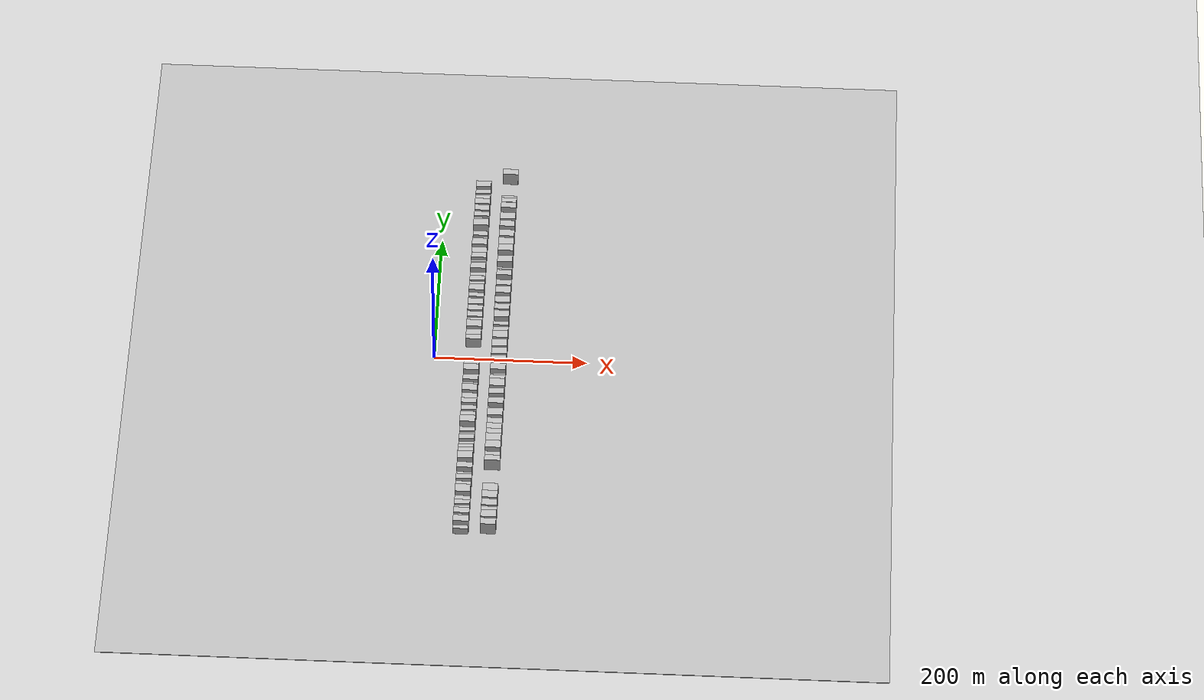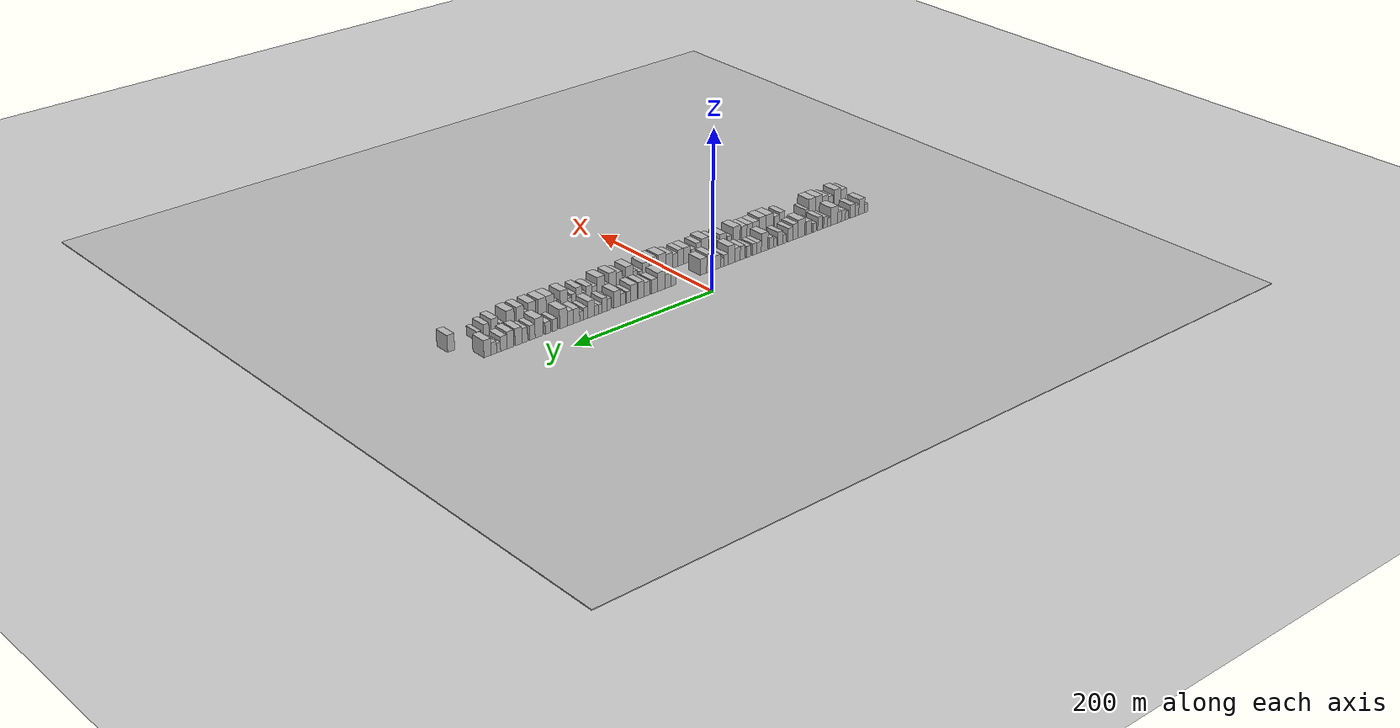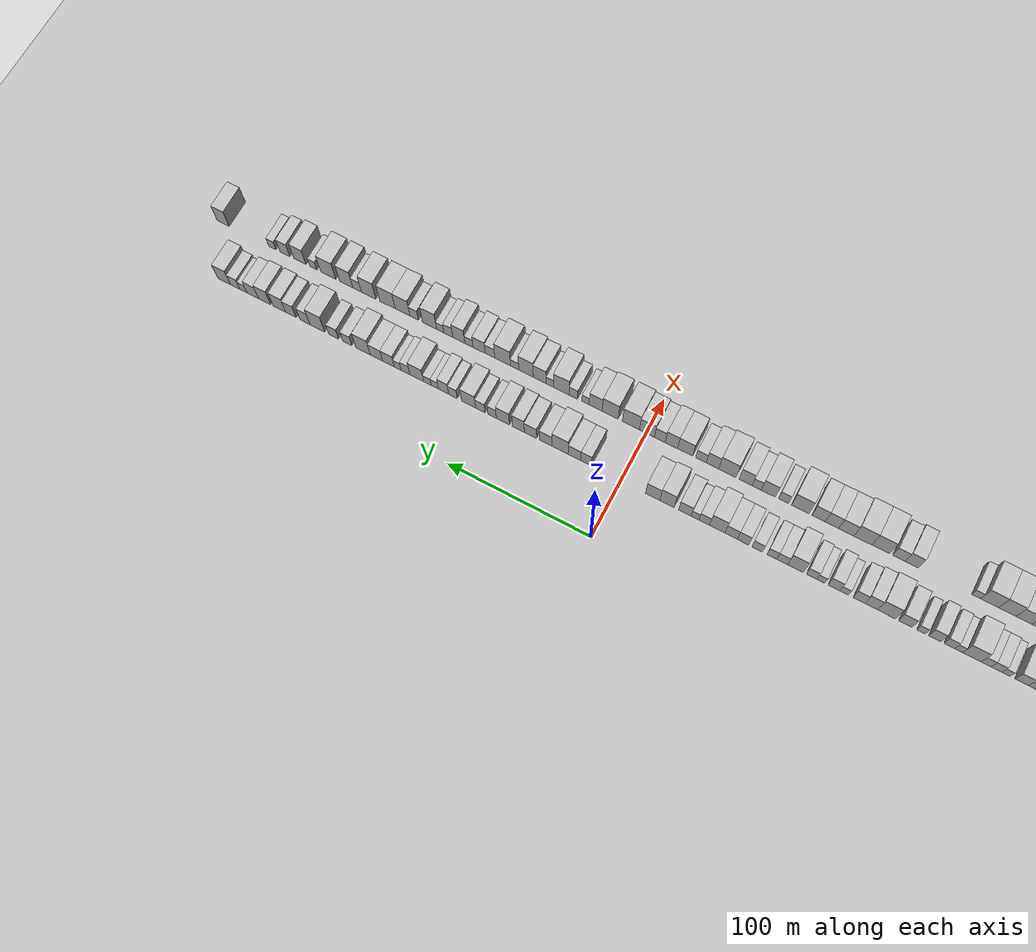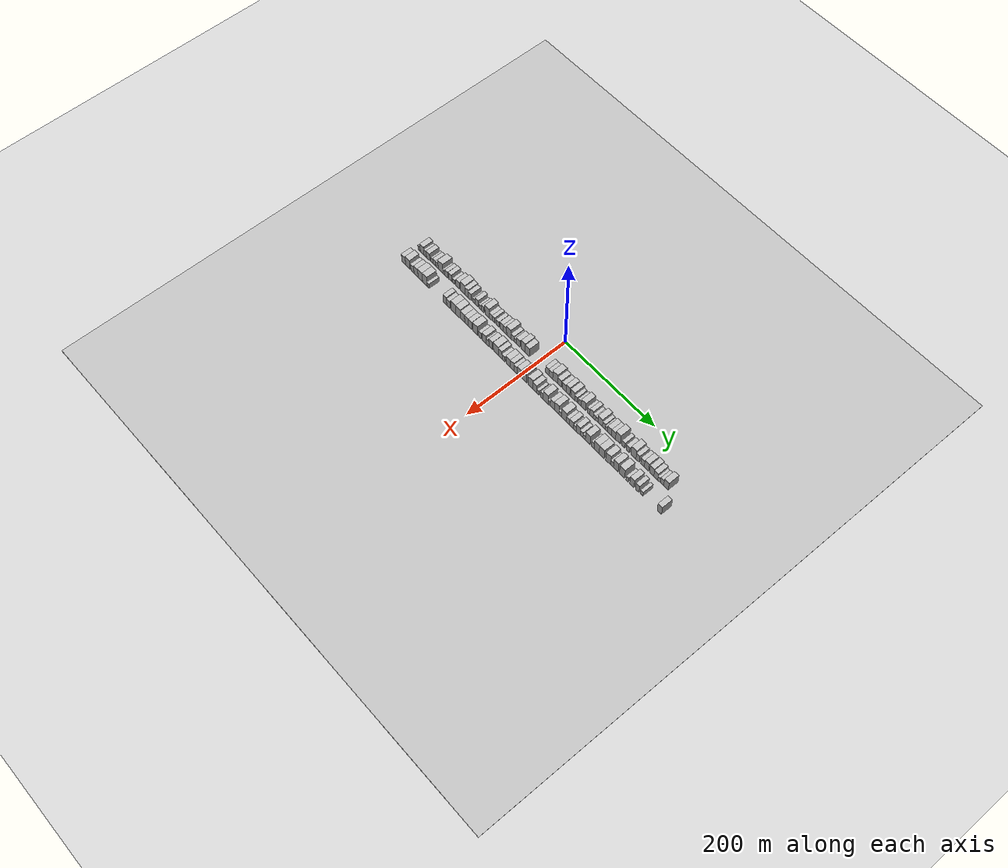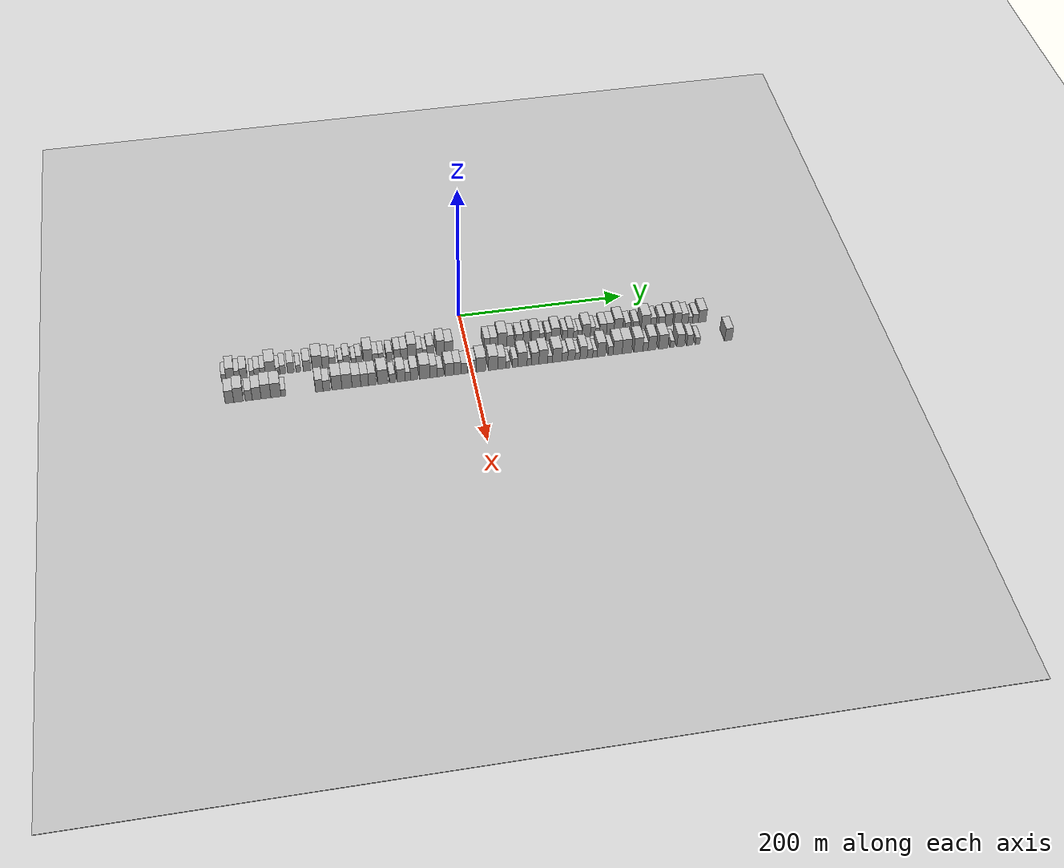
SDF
<?xml version="1.0" encoding="utf-8"?>

<sdf version="1.6">

   <world name="default">

      <gui fullscreen="0">

         <camera name="user_camera">

            <pose>-15 0 4.57585 0 0 0</pose>

            <view_controller>orbit</view_controller>

         </camera>

      </gui>

      <scene>

         <sky>

           <clouds>

             <speed>12</speed>

           </clouds>

         </sky>

         <ambient>0.4 0.4 0.4 1</ambient>

         <background>0.7 0.7 0.7 1</background>

         <shadows>1</shadows>

      </scene>

      <gravity>0 0 -9.8066</gravity>

      <magnetic_field>6e-06 2.3e-05 -4.2e-05</magnetic_field>

      <physics default="0" name="default_physics" type="ode">

         <ode>

            <solver>

               <type>quick</type>

               <iters>10</iters>

               <sor>1.0</sor>

               <use_dynamic_moi_rescaling>0</use_dynamic_moi_rescaling>

            </solver>

            <constraints>

               <cfm>0</cfm>

               <erp>0.2</erp>

               <contact_max_correcting_vel>100</contact_max_correcting_vel>

               <contact_surface_layer>0.001</contact_surface_layer>

            </constraints>

         </ode>

         <max_step_size>0.004</max_step_size>

         <real_time_factor>1</real_time_factor>

         <real_time_update_rate>250</real_time_update_rate>

      </physics>

      <light name="sun" type="directional">

         <cast_shadows>1</cast_shadows>

         <pose>0 0 10 0 0 0</pose>

         <diffuse>0.8 0.8 0.8 1</diffuse>

         <specular>0.2 0.2 0.2 1</specular>

         <attenuation>

            <range>1000</range>

            <constant>0.9</constant>

            <linear>0.01</linear>

            <quadratic>0.001</quadratic>

         </attenuation>

         <direction>-0.5 0.1 -0.9</direction>

      </light>

      <include>

         <name>ground_plane_1</name>

         <uri>model://HANNAS_ground_plane</uri>

         <pose>0 0 0  0 0 0</pose>

      </include>

      <include>

         <name>ground_plane_2</name>

         <uri>model://HANNAS_ground_plane</uri>

         <pose>100 0 0  0 0 0</pose>

      </include>

      <model name="building_1">

         <static>1</static>

         <pose frame="">50.0000 -287.2695 0 0.000000 0.000000 0.000000</pose>

         <link name="link">

            <pose frame="">0 0 6.00 0 0 0</pose>

            <collision name="collision">

               <geometry>

                  <box>

                     <size>20.0000 5.4610 12.0000</size>

                  </box>

               </geometry>

               <max_contacts>10</max_contacts>

               <surface>

                  <contact>

                     <ode/>

                  </contact>

                  <bounce/>

                  <friction>

                     <torsional>

                        <ode/>

                     </torsional>

                     <ode/>

                  </friction>

               </surface>

            </collision>

            <visual name="visual">

               <cast_shadows>0</cast_shadows>

               <geometry>

                  <box>

                     <size>20.0000 5.4610 12.0000</size>

                  </box>

               </geometry>

               <material>

                  <script>

                     <uri>model://HANNAS_wall/materials/scripts</uri>

                     <uri>model://HANNAS_wall/materials/textures</uri>

                     <name>vrc/HANNAS_wall</name>

                  </script>

               </material>

            </visual>

            <self_collide>0</self_collide>

            <enable_wind>0</enable_wind>

            <kinematic>0</kinematic>

         </link>

      </model>

      <model name="building_2">

         <static>1</static>

         <pose frame="">50.0000 -279.6769 0 0.000000 0.000000 0.000000</pose>

         <link name="link">

            <pose frame="">0 0 10.50 0 0 0</pose>

            <collision name="collision">

               <geometry>

                  <box>

                     <size>20.0000 9.7242 21.0000</size>

                  </box>

               </geometry>

               <max_contacts>10</max_contacts>

               <surface>

                  <contact>

                     <ode/>

                  </contact>

                  <bounce/>

                  <friction>

                     <torsional>

                        <ode/>

                     </torsional>

                     <ode/>

                  </friction>

               </surface>

            </collision>

            <visual name="visual">

               <cast_shadows>0</cast_shadows>

               <geometry>

                  <box>

                     <size>20.0000 9.7242 21.0000</size>

                  </box>

               </geometry>

               <material>

                  <script>

                     <uri>model://HANNAS_wall/materials/scripts</uri>

                     <uri>model://HANNAS_wall/materials/textures</uri>

                     <name>vrc/HANNAS_wall</name>

                  </script>

               </material>

            </visual>

            <self_collide>0</self_collide>

            <enable_wind>0</enable_wind>

            <kinematic>0</kinematic>

         </link>

      </model>

      <model name="building_3">

         <static>1</static>

         <pose frame="">50.0000 -271.7212 0 0.000000 0.000000 0.000000</pose>

         <link name="link">

            <pose frame="">0 0 7.50 0 0 0</pose>

            <collision name="collision">

               <geometry>

                  <box>

                     <size>20.0000 6.1871 15.0000</size>

                  </box>

               </geometry>

               <max_contacts>10</max_contacts>

               <surface>

                  <contact>

                     <ode/>

                  </contact>

                  <bounce/>

                  <friction>

                     <torsional>

                        <ode/>

                     </torsional>

                     <ode/>

                  </friction>

               </surface>

            </collision>

            <visual name="visual">

               <cast_shadows>0</cast_shadows>

               <geometry>

                  <box>

                     <size>20.0000 6.1871 15.0000</size>

                  </box>

               </geometry>

               <material>

                  <script>

                     <uri>model://HANNAS_wall/materials/scripts</uri>

                     <uri>model://HANNAS_wall/materials/textures</uri>

                     <name>vrc/HANNAS_wall</name>

                  </script>

               </material>

            </visual>

            <self_collide>0</self_collide>

            <enable_wind>0</enable_wind>

            <kinematic>0</kinematic>

         </link>

      </model>

      <model name="building_4">

         <static>1</static>

         <pose frame="">50.0000 -264.3217 0 0.000000 0.000000 0.000000</pose>

         <link name="link">

            <pose frame="">0 0 9.00 0 0 0</pose>

            <collision name="collision">

               <geometry>

                  <box>

                     <size>20.0000 8.6118 18.0000</size>

                  </box>

               </geometry>

               <max_contacts>10</max_contacts>

               <surface>

                  <contact>

                     <ode/>

                  </contact>

                  <bounce/>

                  <friction>

                     <torsional>

                        <ode/>

                     </torsional>

                     <ode/>

                  </friction>

               </surface>

            </collision>

            <visual name="visual">

               <cast_shadows>0</cast_shadows>

               <geometry>

                  <box>

                     <size>20.0000 8.6118 18.0000</size>

                  </box>

               </geometry>

               <material>

                  <script>

                     <uri>model://HANNAS_wall/materials/scripts</uri>

                     <uri>model://HANNAS_wall/materials/textures</uri>

                     <name>vrc/HANNAS_wall</name>

                  </script>

               </material>

            </visual>

            <self_collide>0</self_collide>

            <enable_wind>0</enable_wind>

            <kinematic>0</kinematic>

         </link>

      </model>

      <model name="building_5">

         <static>1</static>

         <pose frame="">50.0000 -254.4068 0 0.000000 0.000000 0.000000</pose>

         <link name="link">

            <pose frame="">0 0 6.00 0 0 0</pose>

            <collision name="collision">

               <geometry>

                  <box>

                     <size>20.0000 5.2180 12.0000</size>

                  </box>

               </geometry>

               <max_contacts>10</max_contacts>

               <surface>

                  <contact>

                     <ode/>

                  </contact>

                  <bounce/>

                  <friction>

                     <torsional>

                        <ode/>

                     </torsional>

                     <ode/>

                  </friction>

               </surface>

            </collision>

            <visual name="visual">

               <cast_shadows>0</cast_shadows>

               <geometry>

                  <box>

                     <size>20.0000 5.2180 12.0000</size>

                  </box>

               </geometry>

               <material>

                  <script>

                     <uri>model://HANNAS_wall/materials/scripts</uri>

                     <uri>model://HANNAS_wall/materials/textures</uri>

                     <name>vrc/HANNAS_wall</name>

                  </script>

               </material>

            </visual>

            <self_collide>0</self_collide>

            <enable_wind>0</enable_wind>

            <kinematic>0</kinematic>

         </link>

      </model>

      <model name="building_6">

         <static>1</static>

         <pose frame="">50.0000 -248.3889 0 0.000000 0.000000 0.000000</pose>

         <link name="link">

            <pose frame="">0 0 7.50 0 0 0</pose>

            <collision name="collision">

               <geometry>

                  <box>

                     <size>20.0000 6.8179 15.0000</size>

                  </box>

               </geometry>

               <max_contacts>10</max_contacts>

               <surface>

                  <contact>

                     <ode/>

                  </contact>

                  <bounce/>

                  <friction>

                     <torsional>

                        <ode/>

                     </torsional>

                     <ode/>

                  </friction>

               </surface>

            </collision>

            <visual name="visual">

               <cast_shadows>0</cast_shadows>

               <geometry>

                  <box>

                     <size>20.0000 6.8179 15.0000</size>

                  </box>

               </geometry>

               <material>

                  <script>

                     <uri>model://HANNAS_wall/materials/scripts</uri>

                     <uri>model://HANNAS_wall/materials/textures</uri>

                     <name>vrc/HANNAS_wall</name>

                  </script>

               </material>

            </visual>

            <self_collide>0</self_collide>

            <enable_wind>0</enable_wind>

            <kinematic>0</kinematic>

         </link>

      </model>

      <model name="building_7">

         <static>1</static>

         <pose frame="">50.0000 -241.8399 0 0.000000 0.000000 0.000000</pose>

         <link name="link">

            <pose frame="">0 0 7.50 0 0 0</pose>

            <collision name="collision">

               <geometry>

                  <box>

                     <size>20.0000 6.2800 15.0000</size>

                  </box>

               </geometry>

               <max_contacts>10</max_contacts>

               <surface>

                  <contact>

                     <ode/>

                  </contact>

                  <bounce/>

                  <friction>

                     <torsional>

                        <ode/>

                     </torsional>

                     <ode/>

                  </friction>

               </surface>

            </collision>

            <visual name="visual">

               <cast_shadows>0</cast_shadows>

               <geometry>

                  <box>

                     <size>20.0000 6.2800 15.0000</size>

                  </box>

               </geometry>

               <material>

                  <script>

                     <uri>model://HANNAS_wall/materials/scripts</uri>

                     <uri>model://HANNAS_wall/materials/textures</uri>

                     <name>vrc/HANNAS_wall</name>

                  </script>

               </material>

            </visual>

            <self_collide>0</self_collide>

            <enable_wind>0</enable_wind>

            <kinematic>0</kinematic>

         </link>

      </model>

      <model name="building_8">

         <static>1</static>

         <pose frame="">50.0000 -232.7766 0 0.000000 0.000000 0.000000</pose>

         <link name="link">

            <pose frame="">0 0 12.00 0 0 0</pose>

            <collision name="collision">

               <geometry>

                  <box>

                     <size>20.0000 11.8468 24.0000</size>

                  </box>

               </geometry>

               <max_contacts>10</max_contacts>

               <surface>

                  <contact>

                     <ode/>

                  </contact>

                  <bounce/>

                  <friction>

                     <torsional>

                        <ode/>

                     </torsional>

                     <ode/>

                  </friction>

               </surface>

            </collision>

            <visual name="visual">

               <cast_shadows>0</cast_shadows>

               <geometry>

                  <box>

                     <size>20.0000 11.8468 24.0000</size>

                  </box>

               </geometry>

               <material>

                  <script>

                     <uri>model://HANNAS_wall/materials/scripts</uri>

                     <uri>model://HANNAS_wall/materials/textures</uri>

                     <name>vrc/HANNAS_wall</name>

                  </script>

               </material>

            </visual>

            <self_collide>0</self_collide>

            <enable_wind>0</enable_wind>

            <kinematic>0</kinematic>

         </link>

      </model>

      <model name="building_9">

         <static>1</static>

         <pose frame="">50.0000 -224.3368 0 0.000000 0.000000 0.000000</pose>

         <link name="link">

            <pose frame="">0 0 6.00 0 0 0</pose>

            <collision name="collision">

               <geometry>

                  <box>

                     <size>20.0000 5.0327 12.0000</size>

                  </box>

               </geometry>

               <max_contacts>10</max_contacts>

               <surface>

                  <contact>

                     <ode/>

                  </contact>

                  <bounce/>

                  <friction>

                     <torsional>

                        <ode/>

                     </torsional>

                     <ode/>

                  </friction>

               </surface>

            </collision>

            <visual name="visual">

               <cast_shadows>0</cast_shadows>

               <geometry>

                  <box>

                     <size>20.0000 5.0327 12.0000</size>

                  </box>

               </geometry>

               <material>

                  <script>

                     <uri>model://HANNAS_wall/materials/scripts</uri>

                     <uri>model://HANNAS_wall/materials/textures</uri>

                     <name>vrc/HANNAS_wall</name>

                  </script>

               </material>

            </visual>

            <self_collide>0</self_collide>

            <enable_wind>0</enable_wind>

            <kinematic>0</kinematic>

         </link>

      </model>

      <model name="building_10">

         <static>1</static>

         <pose frame="">50.0000 -218.4319 0 0.000000 0.000000 0.000000</pose>

         <link name="link">

            <pose frame="">0 0 7.50 0 0 0</pose>

            <collision name="collision">

               <geometry>

                  <box>

                     <size>20.0000 6.7773 15.0000</size>

                  </box>

               </geometry>

               <max_contacts>10</max_contacts>

               <surface>

                  <contact>

                     <ode/>

                  </contact>

                  <bounce/>

                  <friction>

                     <torsional>

                        <ode/>

                     </torsional>

                     <ode/>

                  </friction>

               </surface>

            </collision>

            <visual name="visual">

               <cast_shadows>0</cast_shadows>

               <geometry>

                  <box>

                     <size>20.0000 6.7773 15.0000</size>

                  </box>

               </geometry>

               <material>

                  <script>

                     <uri>model://HANNAS_wall/materials/scripts</uri>

                     <uri>model://HANNAS_wall/materials/textures</uri>

                     <name>vrc/HANNAS_wall</name>

                  </script>

               </material>

            </visual>

            <self_collide>0</self_collide>

            <enable_wind>0</enable_wind>

            <kinematic>0</kinematic>

         </link>

      </model>

      <model name="building_11">

         <static>1</static>

         <pose frame="">50.0000 -209.1090 0 0.000000 0.000000 0.000000</pose>

         <link name="link">

            <pose frame="">0 0 9.00 0 0 0</pose>

            <collision name="collision">

               <geometry>

                  <box>

                     <size>20.0000 7.8686 18.0000</size>

                  </box>

               </geometry>

               <max_contacts>10</max_contacts>

               <surface>

                  <contact>

                     <ode/>

                  </contact>

                  <bounce/>

                  <friction>

                     <torsional>

                        <ode/>

                     </torsional>

                     <ode/>

                  </friction>

               </surface>

            </collision>

            <visual name="visual">

               <cast_shadows>0</cast_shadows>

               <geometry>

                  <box>

                     <size>20.0000 7.8686 18.0000</size>

                  </box>

               </geometry>

               <material>

                  <script>

                     <uri>model://HANNAS_wall/materials/scripts</uri>

                     <uri>model://HANNAS_wall/materials/textures</uri>

                     <name>vrc/HANNAS_wall</name>

                  </script>

               </material>

            </visual>

            <self_collide>0</self_collide>

            <enable_wind>0</enable_wind>

            <kinematic>0</kinematic>

         </link>

      </model>

      <model name="building_12">

         <static>1</static>

         <pose frame="">50.0000 -200.3443 0 0.000000 0.000000 0.000000</pose>

         <link name="link">

            <pose frame="">0 0 6.00 0 0 0</pose>

            <collision name="collision">

               <geometry>

                  <box>

                     <size>20.0000 5.6607 12.0000</size>

                  </box>

               </geometry>

               <max_contacts>10</max_contacts>

               <surface>

                  <contact>

                     <ode/>

                  </contact>

                  <bounce/>

                  <friction>

                     <torsional>

                        <ode/>

                     </torsional>

                     <ode/>

                  </friction>

               </surface>

            </collision>

            <visual name="visual">

               <cast_shadows>0</cast_shadows>

               <geometry>

                  <box>

                     <size>20.0000 5.6607 12.0000</size>

                  </box>

               </geometry>

               <material>

                  <script>

                     <uri>model://HANNAS_wall/materials/scripts</uri>

                     <uri>model://HANNAS_wall/materials/textures</uri>

                     <name>vrc/HANNAS_wall</name>

                  </script>

               </material>

            </visual>

            <self_collide>0</self_collide>

            <enable_wind>0</enable_wind>

            <kinematic>0</kinematic>

         </link>

      </model>

      <model name="building_13">

         <static>1</static>

         <pose frame="">50.0000 -190.1287 0 0.000000 0.000000 0.000000</pose>

         <link name="link">

            <pose frame="">0 0 9.00 0 0 0</pose>

            <collision name="collision">

               <geometry>

                  <box>

                     <size>20.0000 8.7705 18.0000</size>

                  </box>

               </geometry>

               <max_contacts>10</max_contacts>

               <surface>

                  <contact>

                     <ode/>

                  </contact>

                  <bounce/>

                  <friction>

                     <torsional>

                        <ode/>

                     </torsional>

                     <ode/>

                  </friction>

               </surface>

            </collision>

            <visual name="visual">

               <cast_shadows>0</cast_shadows>

               <geometry>

                  <box>

                     <size>20.0000 8.7705 18.0000</size>

                  </box>

               </geometry>

               <material>

                  <script>

                     <uri>model://HANNAS_wall/materials/scripts</uri>

                     <uri>model://HANNAS_wall/materials/textures</uri>

                     <name>vrc/HANNAS_wall</name>

                  </script>

               </material>

            </visual>

            <self_collide>0</self_collide>

            <enable_wind>0</enable_wind>

            <kinematic>0</kinematic>

         </link>

      </model>

      <model name="building_14">

         <static>1</static>

         <pose frame="">50.0000 -177.9583 0 0.000000 0.000000 0.000000</pose>

         <link name="link">

            <pose frame="">0 0 12.00 0 0 0</pose>

            <collision name="collision">

               <geometry>

                  <box>

                     <size>20.0000 11.5704 24.0000</size>

                  </box>

               </geometry>

               <max_contacts>10</max_contacts>

               <surface>

                  <contact>

                     <ode/>

                  </contact>

                  <bounce/>

                  <friction>

                     <torsional>

                        <ode/>

                     </torsional>

                     <ode/>

                  </friction>

               </surface>

            </collision>

            <visual name="visual">

               <cast_shadows>0</cast_shadows>

               <geometry>

                  <box>

                     <size>20.0000 11.5704 24.0000</size>

                  </box>

               </geometry>

               <material>

                  <script>

                     <uri>model://HANNAS_wall/materials/scripts</uri>

                     <uri>model://HANNAS_wall/materials/textures</uri>

                     <name>vrc/HANNAS_wall</name>

                  </script>

               </material>

            </visual>

            <self_collide>0</self_collide>

            <enable_wind>0</enable_wind>

            <kinematic>0</kinematic>

         </link>

      </model>

      <model name="building_15">

         <static>1</static>

         <pose frame="">50.0000 -167.9573 0 0.000000 0.000000 0.000000</pose>

         <link name="link">

            <pose frame="">0 0 10.50 0 0 0</pose>

            <collision name="collision">

               <geometry>

                  <box>

                     <size>20.0000 8.4315 21.0000</size>

                  </box>

               </geometry>

               <max_contacts>10</max_contacts>

               <surface>

                  <contact>

                     <ode/>

                  </contact>

                  <bounce/>

                  <friction>

                     <torsional>

                        <ode/>

                     </torsional>

                     <ode/>

                  </friction>

               </surface>

            </collision>

            <visual name="visual">

               <cast_shadows>0</cast_shadows>

               <geometry>

                  <box>

                     <size>20.0000 8.4315 21.0000</size>

                  </box>

               </geometry>

               <material>

                  <script>

                     <uri>model://HANNAS_wall/materials/scripts</uri>

                     <uri>model://HANNAS_wall/materials/textures</uri>

                     <name>vrc/HANNAS_wall</name>

                  </script>

               </material>

            </visual>

            <self_collide>0</self_collide>

            <enable_wind>0</enable_wind>

            <kinematic>0</kinematic>

         </link>

      </model>

      <model name="building_16">

         <static>1</static>

         <pose frame="">50.0000 -159.9387 0 0.000000 0.000000 0.000000</pose>

         <link name="link">

            <pose frame="">0 0 9.00 0 0 0</pose>

            <collision name="collision">

               <geometry>

                  <box>

                     <size>20.0000 7.6058 18.0000</size>

                  </box>

               </geometry>

               <max_contacts>10</max_contacts>

               <surface>

                  <contact>

                     <ode/>

                  </contact>

                  <bounce/>

                  <friction>

                     <torsional>

                        <ode/>

                     </torsional>

                     <ode/>

                  </friction>

               </surface>

            </collision>

            <visual name="visual">

               <cast_shadows>0</cast_shadows>

               <geometry>

                  <box>

                     <size>20.0000 7.6058 18.0000</size>

                  </box>

               </geometry>

               <material>

                  <script>

                     <uri>model://HANNAS_wall/materials/scripts</uri>

                     <uri>model://HANNAS_wall/materials/textures</uri>

                     <name>vrc/HANNAS_wall</name>

                  </script>

               </material>

            </visual>

            <self_collide>0</self_collide>

            <enable_wind>0</enable_wind>

            <kinematic>0</kinematic>

         </link>

      </model>

      <model name="building_17">

         <static>1</static>

         <pose frame="">50.0000 -150.2463 0 0.000000 0.000000 0.000000</pose>

         <link name="link">

            <pose frame="">0 0 6.00 0 0 0</pose>

            <collision name="collision">

               <geometry>

                  <box>

                     <size>20.0000 5.7791 12.0000</size>

                  </box>

               </geometry>

               <max_contacts>10</max_contacts>

               <surface>

                  <contact>

                     <ode/>

                  </contact>

                  <bounce/>

                  <friction>

                     <torsional>

                        <ode/>

                     </torsional>

                     <ode/>

                  </friction>

               </surface>

            </collision>

            <visual name="visual">

               <cast_shadows>0</cast_shadows>

               <geometry>

                  <box>

                     <size>20.0000 5.7791 12.0000</size>

                  </box>

               </geometry>

               <material>

                  <script>

                     <uri>model://HANNAS_wall/materials/scripts</uri>

                     <uri>model://HANNAS_wall/materials/textures</uri>

                     <name>vrc/HANNAS_wall</name>

                  </script>

               </material>

            </visual>

            <self_collide>0</self_collide>

            <enable_wind>0</enable_wind>

            <kinematic>0</kinematic>

         </link>

      </model>

      <model name="building_18">

         <static>1</static>

         <pose frame="">50.0000 -143.4901 0 0.000000 0.000000 0.000000</pose>

         <link name="link">

            <pose frame="">0 0 9.00 0 0 0</pose>

            <collision name="collision">

               <geometry>

                  <box>

                     <size>20.0000 7.7331 18.0000</size>

                  </box>

               </geometry>

               <max_contacts>10</max_contacts>

               <surface>

                  <contact>

                     <ode/>

                  </contact>

                  <bounce/>

                  <friction>

                     <torsional>

                        <ode/>

                     </torsional>

                     <ode/>

                  </friction>

               </surface>

            </collision>

            <visual name="visual">

               <cast_shadows>0</cast_shadows>

               <geometry>

                  <box>

                     <size>20.0000 7.7331 18.0000</size>

                  </box>

               </geometry>

               <material>

                  <script>

                     <uri>model://HANNAS_wall/materials/scripts</uri>

                     <uri>model://HANNAS_wall/materials/textures</uri>

                     <name>vrc/HANNAS_wall</name>

                  </script>

               </material>

            </visual>

            <self_collide>0</self_collide>

            <enable_wind>0</enable_wind>

            <kinematic>0</kinematic>

         </link>

      </model>

      <model name="building_19">

         <static>1</static>

         <pose frame="">50.0000 -134.9416 0 0.000000 0.000000 0.000000</pose>

         <link name="link">

            <pose frame="">0 0 6.00 0 0 0</pose>

            <collision name="collision">

               <geometry>

                  <box>

                     <size>20.0000 5.3639 12.0000</size>

                  </box>

               </geometry>

               <max_contacts>10</max_contacts>

               <surface>

                  <contact>

                     <ode/>

                  </contact>

                  <bounce/>

                  <friction>

                     <torsional>

                        <ode/>

                     </torsional>

                     <ode/>

                  </friction>

               </surface>

            </collision>

            <visual name="visual">

               <cast_shadows>0</cast_shadows>

               <geometry>

                  <box>

                     <size>20.0000 5.3639 12.0000</size>

                  </box>

               </geometry>

               <material>

                  <script>

                     <uri>model://HANNAS_wall/materials/scripts</uri>

                     <uri>model://HANNAS_wall/materials/textures</uri>

                     <name>vrc/HANNAS_wall</name>

                  </script>

               </material>

            </visual>

            <self_collide>0</self_collide>

            <enable_wind>0</enable_wind>

            <kinematic>0</kinematic>

         </link>

      </model>

      <model name="building_20">

         <static>1</static>

         <pose frame="">50.0000 -128.8248 0 0.000000 0.000000 0.000000</pose>

         <link name="link">

            <pose frame="">0 0 7.50 0 0 0</pose>

            <collision name="collision">

               <geometry>

                  <box>

                     <size>20.0000 6.8697 15.0000</size>

                  </box>

               </geometry>

               <max_contacts>10</max_contacts>

               <surface>

                  <contact>

                     <ode/>

                  </contact>

                  <bounce/>

                  <friction>

                     <torsional>

                        <ode/>

                     </torsional>

                     <ode/>

                  </friction>

               </surface>

            </collision>

            <visual name="visual">

               <cast_shadows>0</cast_shadows>

               <geometry>

                  <box>

                     <size>20.0000 6.8697 15.0000</size>

                  </box>

               </geometry>

               <material>

                  <script>

                     <uri>model://HANNAS_wall/materials/scripts</uri>

                     <uri>model://HANNAS_wall/materials/textures</uri>

                     <name>vrc/HANNAS_wall</name>

                  </script>

               </material>

            </visual>

            <self_collide>0</self_collide>

            <enable_wind>0</enable_wind>

            <kinematic>0</kinematic>

         </link>

      </model>

      <model name="building_21">

         <static>1</static>

         <pose frame="">50.0000 -118.1324 0 0.000000 0.000000 0.000000</pose>

         <link name="link">

            <pose frame="">0 0 12.00 0 0 0</pose>

            <collision name="collision">

               <geometry>

                  <box>

                     <size>20.0000 10.5152 24.0000</size>

                  </box>

               </geometry>

               <max_contacts>10</max_contacts>

               <surface>

                  <contact>

                     <ode/>

                  </contact>

                  <bounce/>

                  <friction>

                     <torsional>

                        <ode/>

                     </torsional>

                     <ode/>

                  </friction>

               </surface>

            </collision>

            <visual name="visual">

               <cast_shadows>0</cast_shadows>

               <geometry>

                  <box>

                     <size>20.0000 10.5152 24.0000</size>

                  </box>

               </geometry>

               <material>

                  <script>

                     <uri>model://HANNAS_wall/materials/scripts</uri>

                     <uri>model://HANNAS_wall/materials/textures</uri>

                     <name>vrc/HANNAS_wall</name>

                  </script>

               </material>

            </visual>

            <self_collide>0</self_collide>

            <enable_wind>0</enable_wind>

            <kinematic>0</kinematic>

         </link>

      </model>

      <model name="building_22">

         <static>1</static>

         <pose frame="">50.0000 -109.2981 0 0.000000 0.000000 0.000000</pose>

         <link name="link">

            <pose frame="">0 0 7.50 0 0 0</pose>

            <collision name="collision">

               <geometry>

                  <box>

                     <size>20.0000 7.1534 15.0000</size>

                  </box>

               </geometry>

               <max_contacts>10</max_contacts>

               <surface>

                  <contact>

                     <ode/>

                  </contact>

                  <bounce/>

                  <friction>

                     <torsional>

                        <ode/>

                     </torsional>

                     <ode/>

                  </friction>

               </surface>

            </collision>

            <visual name="visual">

               <cast_shadows>0</cast_shadows>

               <geometry>

                  <box>

                     <size>20.0000 7.1534 15.0000</size>

                  </box>

               </geometry>

               <material>

                  <script>

                     <uri>model://HANNAS_wall/materials/scripts</uri>

                     <uri>model://HANNAS_wall/materials/textures</uri>

                     <name>vrc/HANNAS_wall</name>

                  </script>

               </material>

            </visual>

            <self_collide>0</self_collide>

            <enable_wind>0</enable_wind>

            <kinematic>0</kinematic>

         </link>

      </model>

      <model name="building_23">

         <static>1</static>

         <pose frame="">50.0000 -102.4852 0 0.000000 0.000000 0.000000</pose>

         <link name="link">

            <pose frame="">0 0 7.50 0 0 0</pose>

            <collision name="collision">

               <geometry>

                  <box>

                     <size>20.0000 6.4725 15.0000</size>

                  </box>

               </geometry>

               <max_contacts>10</max_contacts>

               <surface>

                  <contact>

                     <ode/>

                  </contact>

                  <bounce/>

                  <friction>

                     <torsional>

                        <ode/>

                     </torsional>

                     <ode/>

                  </friction>

               </surface>

            </collision>

            <visual name="visual">

               <cast_shadows>0</cast_shadows>

               <geometry>

                  <box>

                     <size>20.0000 6.4725 15.0000</size>

                  </box>

               </geometry>

               <material>

                  <script>

                     <uri>model://HANNAS_wall/materials/scripts</uri>

                     <uri>model://HANNAS_wall/materials/textures</uri>

                     <name>vrc/HANNAS_wall</name>

                  </script>

               </material>

            </visual>

            <self_collide>0</self_collide>

            <enable_wind>0</enable_wind>

            <kinematic>0</kinematic>

         </link>

      </model>

      <model name="building_24">

         <static>1</static>

         <pose frame="">50.0000 -92.6460 0 0.000000 0.000000 0.000000</pose>

         <link name="link">

            <pose frame="">0 0 7.50 0 0 0</pose>

            <collision name="collision">

               <geometry>

                  <box>

                     <size>20.0000 7.2058 15.0000</size>

                  </box>

               </geometry>

               <max_contacts>10</max_contacts>

               <surface>

                  <contact>

                     <ode/>

                  </contact>

                  <bounce/>

                  <friction>

                     <torsional>

                        <ode/>

                     </torsional>

                     <ode/>

                  </friction>

               </surface>

            </collision>

            <visual name="visual">

               <cast_shadows>0</cast_shadows>

               <geometry>

                  <box>

                     <size>20.0000 7.2058 15.0000</size>

                  </box>

               </geometry>

               <material>

                  <script>

                     <uri>model://HANNAS_wall/materials/scripts</uri>

                     <uri>model://HANNAS_wall/materials/textures</uri>

                     <name>vrc/HANNAS_wall</name>

                  </script>

               </material>

            </visual>

            <self_collide>0</self_collide>

            <enable_wind>0</enable_wind>

            <kinematic>0</kinematic>

         </link>

      </model>

      <model name="building_25">

         <static>1</static>

         <pose frame="">50.0000 -83.1704 0 0.000000 0.000000 0.000000</pose>

         <link name="link">

            <pose frame="">0 0 9.00 0 0 0</pose>

            <collision name="collision">

               <geometry>

                  <box>

                     <size>20.0000 7.7455 18.0000</size>

                  </box>

               </geometry>

               <max_contacts>10</max_contacts>

               <surface>

                  <contact>

                     <ode/>

                  </contact>

                  <bounce/>

                  <friction>

                     <torsional>

                        <ode/>

                     </torsional>

                     <ode/>

                  </friction>

               </surface>

            </collision>

            <visual name="visual">

               <cast_shadows>0</cast_shadows>

               <geometry>

                  <box>

                     <size>20.0000 7.7455 18.0000</size>

                  </box>

               </geometry>

               <material>

                  <script>

                     <uri>model://HANNAS_wall/materials/scripts</uri>

                     <uri>model://HANNAS_wall/materials/textures</uri>

                     <name>vrc/HANNAS_wall</name>

                  </script>

               </material>

            </visual>

            <self_collide>0</self_collide>

            <enable_wind>0</enable_wind>

            <kinematic>0</kinematic>

         </link>

      </model>

      <model name="building_26">

         <static>1</static>

         <pose frame="">50.0000 -75.1725 0 0.000000 0.000000 0.000000</pose>

         <link name="link">

            <pose frame="">0 0 9.00 0 0 0</pose>

            <collision name="collision">

               <geometry>

                  <box>

                     <size>20.0000 8.2501 18.0000</size>

                  </box>

               </geometry>

               <max_contacts>10</max_contacts>

               <surface>

                  <contact>

                     <ode/>

                  </contact>

                  <bounce/>

                  <friction>

                     <torsional>

                        <ode/>

                     </torsional>

                     <ode/>

                  </friction>

               </surface>

            </collision>

            <visual name="visual">

               <cast_shadows>0</cast_shadows>

               <geometry>

                  <box>

                     <size>20.0000 8.2501 18.0000</size>

                  </box>

               </geometry>

               <material>

                  <script>

                     <uri>model://HANNAS_wall/materials/scripts</uri>

                     <uri>model://HANNAS_wall/materials/textures</uri>

                     <name>vrc/HANNAS_wall</name>

                  </script>

               </material>

            </visual>

            <self_collide>0</self_collide>

            <enable_wind>0</enable_wind>

            <kinematic>0</kinematic>

         </link>

      </model>

      <model name="building_27">

         <static>1</static>

         <pose frame="">50.0000 -65.7889 0 0.000000 0.000000 0.000000</pose>

         <link name="link">

            <pose frame="">0 0 12.00 0 0 0</pose>

            <collision name="collision">

               <geometry>

                  <box>

                     <size>20.0000 10.5172 24.0000</size>

                  </box>

               </geometry>

               <max_contacts>10</max_contacts>

               <surface>

                  <contact>

                     <ode/>

                  </contact>

                  <bounce/>

                  <friction>

                     <torsional>

                        <ode/>

                     </torsional>

                     <ode/>

                  </friction>

               </surface>

            </collision>

            <visual name="visual">

               <cast_shadows>0</cast_shadows>

               <geometry>

                  <box>

                     <size>20.0000 10.5172 24.0000</size>

                  </box>

               </geometry>

               <material>

                  <script>

                     <uri>model://HANNAS_wall/materials/scripts</uri>

                     <uri>model://HANNAS_wall/materials/textures</uri>

                     <name>vrc/HANNAS_wall</name>

                  </script>

               </material>

            </visual>

            <self_collide>0</self_collide>

            <enable_wind>0</enable_wind>

            <kinematic>0</kinematic>

         </link>

      </model>

      <model name="building_28">

         <static>1</static>

         <pose frame="">50.0000 -56.9479 0 0.000000 0.000000 0.000000</pose>

         <link name="link">

            <pose frame="">0 0 7.50 0 0 0</pose>

            <collision name="collision">

               <geometry>

                  <box>

                     <size>20.0000 7.1647 15.0000</size>

                  </box>

               </geometry>

               <max_contacts>10</max_contacts>

               <surface>

                  <contact>

                     <ode/>

                  </contact>

                  <bounce/>

                  <friction>

                     <torsional>

                        <ode/>

                     </torsional>

                     <ode/>

                  </friction>

               </surface>

            </collision>

            <visual name="visual">

               <cast_shadows>0</cast_shadows>

               <geometry>

                  <box>

                     <size>20.0000 7.1647 15.0000</size>

                  </box>

               </geometry>

               <material>

                  <script>

                     <uri>model://HANNAS_wall/materials/scripts</uri>

                     <uri>model://HANNAS_wall/materials/textures</uri>

                     <name>vrc/HANNAS_wall</name>

                  </script>

               </material>

            </visual>

            <self_collide>0</self_collide>

            <enable_wind>0</enable_wind>

            <kinematic>0</kinematic>

         </link>

      </model>

      <model name="building_29">

         <static>1</static>

         <pose frame="">50.0000 -50.7540 0 0.000000 0.000000 0.000000</pose>

         <link name="link">

            <pose frame="">0 0 6.00 0 0 0</pose>

            <collision name="collision">

               <geometry>

                  <box>

                     <size>20.0000 5.2231 12.0000</size>

                  </box>

               </geometry>

               <max_contacts>10</max_contacts>

               <surface>

                  <contact>

                     <ode/>

                  </contact>

                  <bounce/>

                  <friction>

                     <torsional>

                        <ode/>

                     </torsional>

                     <ode/>

                  </friction>

               </surface>

            </collision>

            <visual name="visual">

               <cast_shadows>0</cast_shadows>

               <geometry>

                  <box>

                     <size>20.0000 5.2231 12.0000</size>

                  </box>

               </geometry>

               <material>

                  <script>

                     <uri>model://HANNAS_wall/materials/scripts</uri>

                     <uri>model://HANNAS_wall/materials/textures</uri>

                     <name>vrc/HANNAS_wall</name>

                  </script>

               </material>

            </visual>

            <self_collide>0</self_collide>

            <enable_wind>0</enable_wind>

            <kinematic>0</kinematic>

         </link>

      </model>

      <model name="building_30">

         <static>1</static>

         <pose frame="">50.0000 -43.8688 0 0.000000 0.000000 0.000000</pose>

         <link name="link">

            <pose frame="">0 0 9.00 0 0 0</pose>

            <collision name="collision">

               <geometry>

                  <box>

                     <size>20.0000 8.5474 18.0000</size>

                  </box>

               </geometry>

               <max_contacts>10</max_contacts>

               <surface>

                  <contact>

                     <ode/>

                  </contact>

                  <bounce/>

                  <friction>

                     <torsional>

                        <ode/>

                     </torsional>

                     <ode/>

                  </friction>

               </surface>

            </collision>

            <visual name="visual">

               <cast_shadows>0</cast_shadows>

               <geometry>

                  <box>

                     <size>20.0000 8.5474 18.0000</size>

                  </box>

               </geometry>

               <material>

                  <script>

                     <uri>model://HANNAS_wall/materials/scripts</uri>

                     <uri>model://HANNAS_wall/materials/textures</uri>

                     <name>vrc/HANNAS_wall</name>

                  </script>

               </material>

            </visual>

            <self_collide>0</self_collide>

            <enable_wind>0</enable_wind>

            <kinematic>0</kinematic>

         </link>

      </model>

      <model name="building_31">

         <static>1</static>

         <pose frame="">50.0000 -31.7296 0 0.000000 0.000000 0.000000</pose>

         <link name="link">

            <pose frame="">0 0 12.00 0 0 0</pose>

            <collision name="collision">

               <geometry>

                  <box>

                     <size>20.0000 9.7308 24.0000</size>

                  </box>

               </geometry>

               <max_contacts>10</max_contacts>

               <surface>

                  <contact>

                     <ode/>

                  </contact>

                  <bounce/>

                  <friction>

                     <torsional>

                        <ode/>

                     </torsional>

                     <ode/>

                  </friction>

               </surface>

            </collision>

            <visual name="visual">

               <cast_shadows>0</cast_shadows>

               <geometry>

                  <box>

                     <size>20.0000 9.7308 24.0000</size>

                  </box>

               </geometry>

               <material>

                  <script>

                     <uri>model://HANNAS_wall/materials/scripts</uri>

                     <uri>model://HANNAS_wall/materials/textures</uri>

                     <name>vrc/HANNAS_wall</name>

                  </script>

               </material>

            </visual>

            <self_collide>0</self_collide>

            <enable_wind>0</enable_wind>

            <kinematic>0</kinematic>

         </link>

      </model>

      <model name="building_32">

         <static>1</static>

         <pose frame="">50.0000 -21.9422 0 0.000000 0.000000 0.000000</pose>

         <link name="link">

            <pose frame="">0 0 10.50 0 0 0</pose>

            <collision name="collision">

               <geometry>

                  <box>

                     <size>20.0000 9.8439 21.0000</size>

                  </box>

               </geometry>

               <max_contacts>10</max_contacts>

               <surface>

                  <contact>

                     <ode/>

                  </contact>

                  <bounce/>

                  <friction>

                     <torsional>

                        <ode/>

                     </torsional>

                     <ode/>

                  </friction>

               </surface>

            </collision>

            <visual name="visual">

               <cast_shadows>0</cast_shadows>

               <geometry>

                  <box>

                     <size>20.0000 9.8439 21.0000</size>

                  </box>

               </geometry>

               <material>

                  <script>

                     <uri>model://HANNAS_wall/materials/scripts</uri>

                     <uri>model://HANNAS_wall/materials/textures</uri>

                     <name>vrc/HANNAS_wall</name>

                  </script>

               </material>

            </visual>

            <self_collide>0</self_collide>

            <enable_wind>0</enable_wind>

            <kinematic>0</kinematic>

         </link>

      </model>

      <model name="building_33">

         <static>1</static>

         <pose frame="">50.0000 24.1216 0 0.000000 0.000000 0.000000</pose>

         <link name="link">

            <pose frame="">0 0 9.00 0 0 0</pose>

            <collision name="collision">

               <geometry>

                  <box>

                     <size>20.0000 7.4279 18.0000</size>

                  </box>

               </geometry>

               <max_contacts>10</max_contacts>

               <surface>

                  <contact>

                     <ode/>

                  </contact>

                  <bounce/>

                  <friction>

                     <torsional>

                        <ode/>

                     </torsional>

                     <ode/>

                  </friction>

               </surface>

            </collision>

            <visual name="visual">

               <cast_shadows>0</cast_shadows>

               <geometry>

                  <box>

                     <size>20.0000 7.4279 18.0000</size>

                  </box>

               </geometry>

               <material>

                  <script>

                     <uri>model://HANNAS_wall/materials/scripts</uri>

                     <uri>model://HANNAS_wall/materials/textures</uri>

                     <name>vrc/HANNAS_wall</name>

                  </script>

               </material>

            </visual>

            <self_collide>0</self_collide>

            <enable_wind>0</enable_wind>

            <kinematic>0</kinematic>

         </link>

      </model>

      <model name="building_34">

         <static>1</static>

         <pose frame="">50.0000 32.3131 0 0.000000 0.000000 0.000000</pose>

         <link name="link">

            <pose frame="">0 0 9.00 0 0 0</pose>

            <collision name="collision">

               <geometry>

                  <box>

                     <size>20.0000 8.9552 18.0000</size>

                  </box>

               </geometry>

               <max_contacts>10</max_contacts>

               <surface>

                  <contact>

                     <ode/>

                  </contact>

                  <bounce/>

                  <friction>

                     <torsional>

                        <ode/>

                     </torsional>

                     <ode/>

                  </friction>

               </surface>

            </collision>

            <visual name="visual">

               <cast_shadows>0</cast_shadows>

               <geometry>

                  <box>

                     <size>20.0000 8.9552 18.0000</size>

                  </box>

               </geometry>

               <material>

                  <script>

                     <uri>model://HANNAS_wall/materials/scripts</uri>

                     <uri>model://HANNAS_wall/materials/textures</uri>

                     <name>vrc/HANNAS_wall</name>

                  </script>

               </material>

            </visual>

            <self_collide>0</self_collide>

            <enable_wind>0</enable_wind>

            <kinematic>0</kinematic>

         </link>

      </model>

      <model name="building_35">

         <static>1</static>

         <pose frame="">50.0000 42.4267 0 0.000000 0.000000 0.000000</pose>

         <link name="link">

            <pose frame="">0 0 12.00 0 0 0</pose>

            <collision name="collision">

               <geometry>

                  <box>

                     <size>20.0000 11.2719 24.0000</size>

                  </box>

               </geometry>

               <max_contacts>10</max_contacts>

               <surface>

                  <contact>

                     <ode/>

                  </contact>

                  <bounce/>

                  <friction>

                     <torsional>

                        <ode/>

                     </torsional>

                     <ode/>

                  </friction>

               </surface>

            </collision>

            <visual name="visual">

               <cast_shadows>0</cast_shadows>

               <geometry>

                  <box>

                     <size>20.0000 11.2719 24.0000</size>

                  </box>

               </geometry>

               <material>

                  <script>

                     <uri>model://HANNAS_wall/materials/scripts</uri>

                     <uri>model://HANNAS_wall/materials/textures</uri>

                     <name>vrc/HANNAS_wall</name>

                  </script>

               </material>

            </visual>

            <self_collide>0</self_collide>

            <enable_wind>0</enable_wind>

            <kinematic>0</kinematic>

         </link>

      </model>

      <model name="building_36">

         <static>1</static>

         <pose frame="">50.0000 52.4069 0 0.000000 0.000000 0.000000</pose>

         <link name="link">

            <pose frame="">0 0 9.00 0 0 0</pose>

            <collision name="collision">

               <geometry>

                  <box>

                     <size>20.0000 8.6884 18.0000</size>

                  </box>

               </geometry>

               <max_contacts>10</max_contacts>

               <surface>

                  <contact>

                     <ode/>

                  </contact>

                  <bounce/>

                  <friction>

                     <torsional>

                        <ode/>

                     </torsional>

                     <ode/>

                  </friction>

               </surface>

            </collision>

            <visual name="visual">

               <cast_shadows>0</cast_shadows>

               <geometry>

                  <box>

                     <size>20.0000 8.6884 18.0000</size>

                  </box>

               </geometry>

               <material>

                  <script>

                     <uri>model://HANNAS_wall/materials/scripts</uri>

                     <uri>model://HANNAS_wall/materials/textures</uri>

                     <name>vrc/HANNAS_wall</name>

                  </script>

               </material>

            </visual>

            <self_collide>0</self_collide>

            <enable_wind>0</enable_wind>

            <kinematic>0</kinematic>

         </link>

      </model>

      <model name="building_37">

         <static>1</static>

         <pose frame="">50.0000 63.1032 0 0.000000 0.000000 0.000000</pose>

         <link name="link">

            <pose frame="">0 0 9.00 0 0 0</pose>

            <collision name="collision">

               <geometry>

                  <box>

                     <size>20.0000 8.7043 18.0000</size>

                  </box>

               </geometry>

               <max_contacts>10</max_contacts>

               <surface>

                  <contact>

                     <ode/>

                  </contact>

                  <bounce/>

                  <friction>

                     <torsional>

                        <ode/>

                     </torsional>

                     <ode/>

                  </friction>

               </surface>

            </collision>

            <visual name="visual">

               <cast_shadows>0</cast_shadows>

               <geometry>

                  <box>

                     <size>20.0000 8.7043 18.0000</size>

                  </box>

               </geometry>

               <material>

                  <script>

                     <uri>model://HANNAS_wall/materials/scripts</uri>

                     <uri>model://HANNAS_wall/materials/textures</uri>

                     <name>vrc/HANNAS_wall</name>

                  </script>

               </material>

            </visual>

            <self_collide>0</self_collide>

            <enable_wind>0</enable_wind>

            <kinematic>0</kinematic>

         </link>

      </model>

      <model name="building_38">

         <static>1</static>

         <pose frame="">50.0000 71.6830 0 0.000000 0.000000 0.000000</pose>

         <link name="link">

            <pose frame="">0 0 10.50 0 0 0</pose>

            <collision name="collision">

               <geometry>

                  <box>

                     <size>20.0000 8.4552 21.0000</size>

                  </box>

               </geometry>

               <max_contacts>10</max_contacts>

               <surface>

                  <contact>

                     <ode/>

                  </contact>

                  <bounce/>

                  <friction>

                     <torsional>

                        <ode/>

                     </torsional>

                     <ode/>

                  </friction>

               </surface>

            </collision>

            <visual name="visual">

               <cast_shadows>0</cast_shadows>

               <geometry>

                  <box>

                     <size>20.0000 8.4552 21.0000</size>

                  </box>

               </geometry>

               <material>

                  <script>

                     <uri>model://HANNAS_wall/materials/scripts</uri>

                     <uri>model://HANNAS_wall/materials/textures</uri>

                     <name>vrc/HANNAS_wall</name>

                  </script>

               </material>

            </visual>

            <self_collide>0</self_collide>

            <enable_wind>0</enable_wind>

            <kinematic>0</kinematic>

         </link>

      </model>

      <model name="building_39">

         <static>1</static>

         <pose frame="">50.0000 82.6132 0 0.000000 0.000000 0.000000</pose>

         <link name="link">

            <pose frame="">0 0 10.50 0 0 0</pose>

            <collision name="collision">

               <geometry>

                  <box>

                     <size>20.0000 9.4053 21.0000</size>

                  </box>

               </geometry>

               <max_contacts>10</max_contacts>

               <surface>

                  <contact>

                     <ode/>

                  </contact>

                  <bounce/>

                  <friction>

                     <torsional>

                        <ode/>

                     </torsional>

                     <ode/>

                  </friction>

               </surface>

            </collision>

            <visual name="visual">

               <cast_shadows>0</cast_shadows>

               <geometry>

                  <box>

                     <size>20.0000 9.4053 21.0000</size>

                  </box>

               </geometry>

               <material>

                  <script>

                     <uri>model://HANNAS_wall/materials/scripts</uri>

                     <uri>model://HANNAS_wall/materials/textures</uri>

                     <name>vrc/HANNAS_wall</name>

                  </script>

               </material>

            </visual>

            <self_collide>0</self_collide>

            <enable_wind>0</enable_wind>

            <kinematic>0</kinematic>

         </link>

      </model>

      <model name="building_40">

         <static>1</static>

         <pose frame="">50.0000 90.3303 0 0.000000 0.000000 0.000000</pose>

         <link name="link">

            <pose frame="">0 0 7.50 0 0 0</pose>

            <collision name="collision">

               <geometry>

                  <box>

                     <size>20.0000 6.0289 15.0000</size>

                  </box>

               </geometry>

               <max_contacts>10</max_contacts>

               <surface>

                  <contact>

                     <ode/>

                  </contact>

                  <bounce/>

                  <friction>

                     <torsional>

                        <ode/>

                     </torsional>

                     <ode/>

                  </friction>

               </surface>

            </collision>

            <visual name="visual">

               <cast_shadows>0</cast_shadows>

               <geometry>

                  <box>

                     <size>20.0000 6.0289 15.0000</size>

                  </box>

               </geometry>

               <material>

                  <script>

                     <uri>model://HANNAS_wall/materials/scripts</uri>

                     <uri>model://HANNAS_wall/materials/textures</uri>

                     <name>vrc/HANNAS_wall</name>

                  </script>

               </material>

            </visual>

            <self_collide>0</self_collide>

            <enable_wind>0</enable_wind>

            <kinematic>0</kinematic>

         </link>

      </model>

      <model name="building_41">

         <static>1</static>

         <pose frame="">50.0000 98.6847 0 0.000000 0.000000 0.000000</pose>

         <link name="link">

            <pose frame="">0 0 7.50 0 0 0</pose>

            <collision name="collision">

               <geometry>

                  <box>

                     <size>20.0000 6.6799 15.0000</size>

                  </box>

               </geometry>

               <max_contacts>10</max_contacts>

               <surface>

                  <contact>

                     <ode/>

                  </contact>

                  <bounce/>

                  <friction>

                     <torsional>

                        <ode/>

                     </torsional>

                     <ode/>

                  </friction>

               </surface>

            </collision>

            <visual name="visual">

               <cast_shadows>0</cast_shadows>

               <geometry>

                  <box>

                     <size>20.0000 6.6799 15.0000</size>

                  </box>

               </geometry>

               <material>

                  <script>

                     <uri>model://HANNAS_wall/materials/scripts</uri>

                     <uri>model://HANNAS_wall/materials/textures</uri>

                     <name>vrc/HANNAS_wall</name>

                  </script>

               </material>

            </visual>

            <self_collide>0</self_collide>

            <enable_wind>0</enable_wind>

            <kinematic>0</kinematic>

         </link>

      </model>

      <model name="building_42">

         <static>1</static>

         <pose frame="">50.0000 107.1087 0 0.000000 0.000000 0.000000</pose>

         <link name="link">

            <pose frame="">0 0 10.50 0 0 0</pose>

            <collision name="collision">

               <geometry>

                  <box>

                     <size>20.0000 10.1681 21.0000</size>

                  </box>

               </geometry>

               <max_contacts>10</max_contacts>

               <surface>

                  <contact>

                     <ode/>

                  </contact>

                  <bounce/>

                  <friction>

                     <torsional>

                        <ode/>

                     </torsional>

                     <ode/>

                  </friction>

               </surface>

            </collision>

            <visual name="visual">

               <cast_shadows>0</cast_shadows>

               <geometry>

                  <box>

                     <size>20.0000 10.1681 21.0000</size>

                  </box>

               </geometry>

               <material>

                  <script>

                     <uri>model://HANNAS_wall/materials/scripts</uri>

                     <uri>model://HANNAS_wall/materials/textures</uri>

                     <name>vrc/HANNAS_wall</name>

                  </script>

               </material>

            </visual>

            <self_collide>0</self_collide>

            <enable_wind>0</enable_wind>

            <kinematic>0</kinematic>

         </link>

      </model>

      <model name="building_43">

         <static>1</static>

         <pose frame="">50.0000 118.2897 0 0.000000 0.000000 0.000000</pose>

         <link name="link">

            <pose frame="">0 0 7.50 0 0 0</pose>

            <collision name="collision">

               <geometry>

                  <box>

                     <size>20.0000 6.1939 15.0000</size>

                  </box>

               </geometry>

               <max_contacts>10</max_contacts>

               <surface>

                  <contact>

                     <ode/>

                  </contact>

                  <bounce/>

                  <friction>

                     <torsional>

                        <ode/>

                     </torsional>

                     <ode/>

                  </friction>

               </surface>

            </collision>

            <visual name="visual">

               <cast_shadows>0</cast_shadows>

               <geometry>

                  <box>

                     <size>20.0000 6.1939 15.0000</size>

                  </box>

               </geometry>

               <material>

                  <script>

                     <uri>model://HANNAS_wall/materials/scripts</uri>

                     <uri>model://HANNAS_wall/materials/textures</uri>

                     <name>vrc/HANNAS_wall</name>

                  </script>

               </material>

            </visual>

            <self_collide>0</self_collide>

            <enable_wind>0</enable_wind>

            <kinematic>0</kinematic>

         </link>

      </model>

      <model name="building_44">

         <static>1</static>

         <pose frame="">50.0000 125.0838 0 0.000000 0.000000 0.000000</pose>

         <link name="link">

            <pose frame="">0 0 9.00 0 0 0</pose>

            <collision name="collision">

               <geometry>

                  <box>

                     <size>20.0000 7.3944 18.0000</size>

                  </box>

               </geometry>

               <max_contacts>10</max_contacts>

               <surface>

                  <contact>

                     <ode/>

                  </contact>

                  <bounce/>

                  <friction>

                     <torsional>

                        <ode/>

                     </torsional>

                     <ode/>

                  </friction>

               </surface>

            </collision>

            <visual name="visual">

               <cast_shadows>0</cast_shadows>

               <geometry>

                  <box>

                     <size>20.0000 7.3944 18.0000</size>

                  </box>

               </geometry>

               <material>

                  <script>

                     <uri>model://HANNAS_wall/materials/scripts</uri>

                     <uri>model://HANNAS_wall/materials/textures</uri>

                     <name>vrc/HANNAS_wall</name>

                  </script>

               </material>

            </visual>

            <self_collide>0</self_collide>

            <enable_wind>0</enable_wind>

            <kinematic>0</kinematic>

         </link>

      </model>

      <model name="building_45">

         <static>1</static>

         <pose frame="">50.0000 131.3723 0 0.000000 0.000000 0.000000</pose>

         <link name="link">

            <pose frame="">0 0 6.00 0 0 0</pose>

            <collision name="collision">

               <geometry>

                  <box>

                     <size>20.0000 5.1827 12.0000</size>

                  </box>

               </geometry>

               <max_contacts>10</max_contacts>

               <surface>

                  <contact>

                     <ode/>

                  </contact>

                  <bounce/>

                  <friction>

                     <torsional>

                        <ode/>

                     </torsional>

                     <ode/>

                  </friction>

               </surface>

            </collision>

            <visual name="visual">

               <cast_shadows>0</cast_shadows>

               <geometry>

                  <box>

                     <size>20.0000 5.1827 12.0000</size>

                  </box>

               </geometry>

               <material>

                  <script>

                     <uri>model://HANNAS_wall/materials/scripts</uri>

                     <uri>model://HANNAS_wall/materials/textures</uri>

                     <name>vrc/HANNAS_wall</name>

                  </script>

               </material>

            </visual>

            <self_collide>0</self_collide>

            <enable_wind>0</enable_wind>

            <kinematic>0</kinematic>

         </link>

      </model>

      <model name="building_46">

         <static>1</static>

         <pose frame="">50.0000 136.6902 0 0.000000 0.000000 0.000000</pose>

         <link name="link">

            <pose frame="">0 0 6.00 0 0 0</pose>

            <collision name="collision">

               <geometry>

                  <box>

                     <size>20.0000 5.4529 12.0000</size>

                  </box>

               </geometry>

               <max_contacts>10</max_contacts>

               <surface>

                  <contact>

                     <ode/>

                  </contact>

                  <bounce/>

                  <friction>

                     <torsional>

                        <ode/>

                     </torsional>

                     <ode/>

                  </friction>

               </surface>

            </collision>

            <visual name="visual">

               <cast_shadows>0</cast_shadows>

               <geometry>

                  <box>

                     <size>20.0000 5.4529 12.0000</size>

                  </box>

               </geometry>

               <material>

                  <script>

                     <uri>model://HANNAS_wall/materials/scripts</uri>

                     <uri>model://HANNAS_wall/materials/textures</uri>

                     <name>vrc/HANNAS_wall</name>

                  </script>

               </material>

            </visual>

            <self_collide>0</self_collide>

            <enable_wind>0</enable_wind>

            <kinematic>0</kinematic>

         </link>

      </model>

      <model name="building_47">

         <static>1</static>

         <pose frame="">50.0000 144.4189 0 0.000000 0.000000 0.000000</pose>

         <link name="link">

            <pose frame="">0 0 10.50 0 0 0</pose>

            <collision name="collision">

               <geometry>

                  <box>

                     <size>20.0000 10.0046 21.0000</size>

                  </box>

               </geometry>

               <max_contacts>10</max_contacts>

               <surface>

                  <contact>

                     <ode/>

                  </contact>

                  <bounce/>

                  <friction>

                     <torsional>

                        <ode/>

                     </torsional>

                     <ode/>

                  </friction>

               </surface>

            </collision>

            <visual name="visual">

               <cast_shadows>0</cast_shadows>

               <geometry>

                  <box>

                     <size>20.0000 10.0046 21.0000</size>

                  </box>

               </geometry>

               <material>

                  <script>

                     <uri>model://HANNAS_wall/materials/scripts</uri>

                     <uri>model://HANNAS_wall/materials/textures</uri>

                     <name>vrc/HANNAS_wall</name>

                  </script>

               </material>

            </visual>

            <self_collide>0</self_collide>

            <enable_wind>0</enable_wind>

            <kinematic>0</kinematic>

         </link>

      </model>

      <model name="building_48">

         <static>1</static>

         <pose frame="">50.0000 152.5512 0 0.000000 0.000000 0.000000</pose>

         <link name="link">

            <pose frame="">0 0 7.50 0 0 0</pose>

            <collision name="collision">

               <geometry>

                  <box>

                     <size>20.0000 6.2600 15.0000</size>

                  </box>

               </geometry>

               <max_contacts>10</max_contacts>

               <surface>

                  <contact>

                     <ode/>

                  </contact>

                  <bounce/>

                  <friction>

                     <torsional>

                        <ode/>

                     </torsional>

                     <ode/>

                  </friction>

               </surface>

            </collision>

            <visual name="visual">

               <cast_shadows>0</cast_shadows>

               <geometry>

                  <box>

                     <size>20.0000 6.2600 15.0000</size>

                  </box>

               </geometry>

               <material>

                  <script>

                     <uri>model://HANNAS_wall/materials/scripts</uri>

                     <uri>model://HANNAS_wall/materials/textures</uri>

                     <name>vrc/HANNAS_wall</name>

                  </script>

               </material>

            </visual>

            <self_collide>0</self_collide>

            <enable_wind>0</enable_wind>

            <kinematic>0</kinematic>

         </link>

      </model>

      <model name="building_49">

         <static>1</static>

         <pose frame="">50.0000 158.2031 0 0.000000 0.000000 0.000000</pose>

         <link name="link">

            <pose frame="">0 0 6.00 0 0 0</pose>

            <collision name="collision">

               <geometry>

                  <box>

                     <size>20.0000 5.0439 12.0000</size>

                  </box>

               </geometry>

               <max_contacts>10</max_contacts>

               <surface>

                  <contact>

                     <ode/>

                  </contact>

                  <bounce/>

                  <friction>

                     <torsional>

                        <ode/>

                     </torsional>

                     <ode/>

                  </friction>

               </surface>

            </collision>

            <visual name="visual">

               <cast_shadows>0</cast_shadows>

               <geometry>

                  <box>

                     <size>20.0000 5.0439 12.0000</size>

                  </box>

               </geometry>

               <material>

                  <script>

                     <uri>model://HANNAS_wall/materials/scripts</uri>

                     <uri>model://HANNAS_wall/materials/textures</uri>

                     <name>vrc/HANNAS_wall</name>

                  </script>

               </material>

            </visual>

            <self_collide>0</self_collide>

            <enable_wind>0</enable_wind>

            <kinematic>0</kinematic>

         </link>

      </model>

      <model name="building_50">

         <static>1</static>

         <pose frame="">50.0000 165.0175 0 0.000000 0.000000 0.000000</pose>

         <link name="link">

            <pose frame="">0 0 9.00 0 0 0</pose>

            <collision name="collision">

               <geometry>

                  <box>

                     <size>20.0000 8.5849 18.0000</size>

                  </box>

               </geometry>

               <max_contacts>10</max_contacts>

               <surface>

                  <contact>

                     <ode/>

                  </contact>

                  <bounce/>

                  <friction>

                     <torsional>

                        <ode/>

                     </torsional>

                     <ode/>

                  </friction>

               </surface>

            </collision>

            <visual name="visual">

               <cast_shadows>0</cast_shadows>

               <geometry>

                  <box>

                     <size>20.0000 8.5849 18.0000</size>

                  </box>

               </geometry>

               <material>

                  <script>

                     <uri>model://HANNAS_wall/materials/scripts</uri>

                     <uri>model://HANNAS_wall/materials/textures</uri>

                     <name>vrc/HANNAS_wall</name>

                  </script>

               </material>

            </visual>

            <self_collide>0</self_collide>

            <enable_wind>0</enable_wind>

            <kinematic>0</kinematic>

         </link>

      </model>

      <model name="building_51">

         <static>1</static>

         <pose frame="">50.0000 173.7767 0 0.000000 0.000000 0.000000</pose>

         <link name="link">

            <pose frame="">0 0 9.00 0 0 0</pose>

            <collision name="collision">

               <geometry>

                  <box>

                     <size>20.0000 8.9335 18.0000</size>

                  </box>

               </geometry>

               <max_contacts>10</max_contacts>

               <surface>

                  <contact>

                     <ode/>

                  </contact>

                  <bounce/>

                  <friction>

                     <torsional>

                        <ode/>

                     </torsional>

                     <ode/>

                  </friction>

               </surface>

            </collision>

            <visual name="visual">

               <cast_shadows>0</cast_shadows>

               <geometry>

                  <box>

                     <size>20.0000 8.9335 18.0000</size>

                  </box>

               </geometry>

               <material>

                  <script>

                     <uri>model://HANNAS_wall/materials/scripts</uri>

                     <uri>model://HANNAS_wall/materials/textures</uri>

                     <name>vrc/HANNAS_wall</name>

                  </script>

               </material>

            </visual>

            <self_collide>0</self_collide>

            <enable_wind>0</enable_wind>

            <kinematic>0</kinematic>

         </link>

      </model>

      <model name="building_52">

         <static>1</static>

         <pose frame="">50.0000 183.5678 0 0.000000 0.000000 0.000000</pose>

         <link name="link">

            <pose frame="">0 0 12.00 0 0 0</pose>

            <collision name="collision">

               <geometry>

                  <box>

                     <size>20.0000 10.6486 24.0000</size>

                  </box>

               </geometry>

               <max_contacts>10</max_contacts>

               <surface>

                  <contact>

                     <ode/>

                  </contact>

                  <bounce/>

                  <friction>

                     <torsional>

                        <ode/>

                     </torsional>

                     <ode/>

                  </friction>

               </surface>

            </collision>

            <visual name="visual">

               <cast_shadows>0</cast_shadows>

               <geometry>

                  <box>

                     <size>20.0000 10.6486 24.0000</size>

                  </box>

               </geometry>

               <material>

                  <script>

                     <uri>model://HANNAS_wall/materials/scripts</uri>

                     <uri>model://HANNAS_wall/materials/textures</uri>

                     <name>vrc/HANNAS_wall</name>

                  </script>

               </material>

            </visual>

            <self_collide>0</self_collide>

            <enable_wind>0</enable_wind>

            <kinematic>0</kinematic>

         </link>

      </model>

      <model name="building_53">

         <static>1</static>

         <pose frame="">50.0000 195.2823 0 0.000000 0.000000 0.000000</pose>

         <link name="link">

            <pose frame="">0 0 7.50 0 0 0</pose>

            <collision name="collision">

               <geometry>

                  <box>

                     <size>20.0000 6.7804 15.0000</size>

                  </box>

               </geometry>

               <max_contacts>10</max_contacts>

               <surface>

                  <contact>

                     <ode/>

                  </contact>

                  <bounce/>

                  <friction>

                     <torsional>

                        <ode/>

                     </torsional>

                     <ode/>

                  </friction>

               </surface>

            </collision>

            <visual name="visual">

               <cast_shadows>0</cast_shadows>

               <geometry>

                  <box>

                     <size>20.0000 6.7804 15.0000</size>

                  </box>

               </geometry>

               <material>

                  <script>

                     <uri>model://HANNAS_wall/materials/scripts</uri>

                     <uri>model://HANNAS_wall/materials/textures</uri>

                     <name>vrc/HANNAS_wall</name>

                  </script>

               </material>

            </visual>

            <self_collide>0</self_collide>

            <enable_wind>0</enable_wind>

            <kinematic>0</kinematic>

         </link>

      </model>

      <model name="building_54">

         <static>1</static>

         <pose frame="">50.0000 205.2796 0 0.000000 0.000000 0.000000</pose>

         <link name="link">

            <pose frame="">0 0 7.50 0 0 0</pose>

            <collision name="collision">

               <geometry>

                  <box>

                     <size>20.0000 7.2143 15.0000</size>

                  </box>

               </geometry>

               <max_contacts>10</max_contacts>

               <surface>

                  <contact>

                     <ode/>

                  </contact>

                  <bounce/>

                  <friction>

                     <torsional>

                        <ode/>

                     </torsional>

                     <ode/>

                  </friction>

               </surface>

            </collision>

            <visual name="visual">

               <cast_shadows>0</cast_shadows>

               <geometry>

                  <box>

                     <size>20.0000 7.2143 15.0000</size>

                  </box>

               </geometry>

               <material>

                  <script>

                     <uri>model://HANNAS_wall/materials/scripts</uri>

                     <uri>model://HANNAS_wall/materials/textures</uri>

                     <name>vrc/HANNAS_wall</name>

                  </script>

               </material>

            </visual>

            <self_collide>0</self_collide>

            <enable_wind>0</enable_wind>

            <kinematic>0</kinematic>

         </link>

      </model>

      <model name="building_55">

         <static>1</static>

         <pose frame="">50.0000 217.4143 0 0.000000 0.000000 0.000000</pose>

         <link name="link">

            <pose frame="">0 0 12.00 0 0 0</pose>

            <collision name="collision">

               <geometry>

                  <box>

                     <size>20.0000 11.0549 24.0000</size>

                  </box>

               </geometry>

               <max_contacts>10</max_contacts>

               <surface>

                  <contact>

                     <ode/>

                  </contact>

                  <bounce/>

                  <friction>

                     <torsional>

                        <ode/>

                     </torsional>

                     <ode/>

                  </friction>

               </surface>

            </collision>

            <visual name="visual">

               <cast_shadows>0</cast_shadows>

               <geometry>

                  <box>

                     <size>20.0000 11.0549 24.0000</size>

                  </box>

               </geometry>

               <material>

                  <script>

                     <uri>model://HANNAS_wall/materials/scripts</uri>

                     <uri>model://HANNAS_wall/materials/textures</uri>

                     <name>vrc/HANNAS_wall</name>

                  </script>

               </material>

            </visual>

            <self_collide>0</self_collide>

            <enable_wind>0</enable_wind>

            <kinematic>0</kinematic>

         </link>

      </model>

      <model name="building_56">

         <static>1</static>

         <pose frame="">50.0000 226.5617 0 0.000000 0.000000 0.000000</pose>

         <link name="link">

            <pose frame="">0 0 9.00 0 0 0</pose>

            <collision name="collision">

               <geometry>

                  <box>

                     <size>20.0000 7.2400 18.0000</size>

                  </box>

               </geometry>

               <max_contacts>10</max_contacts>

               <surface>

                  <contact>

                     <ode/>

                  </contact>

                  <bounce/>

                  <friction>

                     <torsional>

                        <ode/>

                     </torsional>

                     <ode/>

                  </friction>

               </surface>

            </collision>

            <visual name="visual">

               <cast_shadows>0</cast_shadows>

               <geometry>

                  <box>

                     <size>20.0000 7.2400 18.0000</size>

                  </box>

               </geometry>

               <material>

                  <script>

                     <uri>model://HANNAS_wall/materials/scripts</uri>

                     <uri>model://HANNAS_wall/materials/textures</uri>

                     <name>vrc/HANNAS_wall</name>

                  </script>

               </material>

            </visual>

            <self_collide>0</self_collide>

            <enable_wind>0</enable_wind>

            <kinematic>0</kinematic>

         </link>

      </model>

      <model name="building_57">

         <static>1</static>

         <pose frame="">50.0000 237.0375 0 0.000000 0.000000 0.000000</pose>

         <link name="link">

            <pose frame="">0 0 9.00 0 0 0</pose>

            <collision name="collision">

               <geometry>

                  <box>

                     <size>20.0000 7.7115 18.0000</size>

                  </box>

               </geometry>

               <max_contacts>10</max_contacts>

               <surface>

                  <contact>

                     <ode/>

                  </contact>

                  <bounce/>

                  <friction>

                     <torsional>

                        <ode/>

                     </torsional>

                     <ode/>

                  </friction>

               </surface>

            </collision>

            <visual name="visual">

               <cast_shadows>0</cast_shadows>

               <geometry>

                  <box>

                     <size>20.0000 7.7115 18.0000</size>

                  </box>

               </geometry>

               <material>

                  <script>

                     <uri>model://HANNAS_wall/materials/scripts</uri>

                     <uri>model://HANNAS_wall/materials/textures</uri>

                     <name>vrc/HANNAS_wall</name>

                  </script>

               </material>

            </visual>

            <self_collide>0</self_collide>

            <enable_wind>0</enable_wind>

            <kinematic>0</kinematic>

         </link>

      </model>

      <model name="building_58">

         <static>1</static>

         <pose frame="">50.0000 245.5695 0 0.000000 0.000000 0.000000</pose>

         <link name="link">

            <pose frame="">0 0 10.50 0 0 0</pose>

            <collision name="collision">

               <geometry>

                  <box>

                     <size>20.0000 9.3526 21.0000</size>

                  </box>

               </geometry>

               <max_contacts>10</max_contacts>

               <surface>

                  <contact>

                     <ode/>

                  </contact>

                  <bounce/>

                  <friction>

                     <torsional>

                        <ode/>

                     </torsional>

                     <ode/>

                  </friction>

               </surface>

            </collision>

            <visual name="visual">

               <cast_shadows>0</cast_shadows>

               <geometry>

                  <box>

                     <size>20.0000 9.3526 21.0000</size>

                  </box>

               </geometry>

               <material>

                  <script>

                     <uri>model://HANNAS_wall/materials/scripts</uri>

                     <uri>model://HANNAS_wall/materials/textures</uri>

                     <name>vrc/HANNAS_wall</name>

                  </script>

               </material>

            </visual>

            <self_collide>0</self_collide>

            <enable_wind>0</enable_wind>

            <kinematic>0</kinematic>

         </link>

      </model>

      <model name="building_59">

         <static>1</static>

         <pose frame="">50.0000 256.7958 0 0.000000 0.000000 0.000000</pose>

         <link name="link">

            <pose frame="">0 0 10.50 0 0 0</pose>

            <collision name="collision">

               <geometry>

                  <box>

                     <size>20.0000 9.1001 21.0000</size>

                  </box>

               </geometry>

               <max_contacts>10</max_contacts>

               <surface>

                  <contact>

                     <ode/>

                  </contact>

                  <bounce/>

                  <friction>

                     <torsional>

                        <ode/>

                     </torsional>

                     <ode/>

                  </friction>

               </surface>

            </collision>

            <visual name="visual">

               <cast_shadows>0</cast_shadows>

               <geometry>

                  <box>

                     <size>20.0000 9.1001 21.0000</size>

                  </box>

               </geometry>

               <material>

                  <script>

                     <uri>model://HANNAS_wall/materials/scripts</uri>

                     <uri>model://HANNAS_wall/materials/textures</uri>

                     <name>vrc/HANNAS_wall</name>

                  </script>

               </material>

            </visual>

            <self_collide>0</self_collide>

            <enable_wind>0</enable_wind>

            <kinematic>0</kinematic>

         </link>

      </model>

      <model name="building_60">

         <static>1</static>

         <pose frame="">50.0000 265.6033 0 0.000000 0.000000 0.000000</pose>

         <link name="link">

            <pose frame="">0 0 9.00 0 0 0</pose>

            <collision name="collision">

               <geometry>

                  <box>

                     <size>20.0000 8.5148 18.0000</size>

                  </box>

               </geometry>

               <max_contacts>10</max_contacts>

               <surface>

                  <contact>

                     <ode/>

                  </contact>

                  <bounce/>

                  <friction>

                     <torsional>

                        <ode/>

                     </torsional>

                     <ode/>

                  </friction>

               </surface>

            </collision>

            <visual name="visual">

               <cast_shadows>0</cast_shadows>

               <geometry>

                  <box>

                     <size>20.0000 8.5148 18.0000</size>

                  </box>

               </geometry>

               <material>

                  <script>

                     <uri>model://HANNAS_wall/materials/scripts</uri>

                     <uri>model://HANNAS_wall/materials/textures</uri>

                     <name>vrc/HANNAS_wall</name>

                  </script>

               </material>

            </visual>

            <self_collide>0</self_collide>

            <enable_wind>0</enable_wind>

            <kinematic>0</kinematic>

         </link>

      </model>

      <model name="building_61">

         <static>1</static>

         <pose frame="">50.0000 272.5477 0 0.000000 0.000000 0.000000</pose>

         <link name="link">

            <pose frame="">0 0 6.00 0 0 0</pose>

            <collision name="collision">

               <geometry>

                  <box>

                     <size>20.0000 5.3740 12.0000</size>

                  </box>

               </geometry>

               <max_contacts>10</max_contacts>

               <surface>

                  <contact>

                     <ode/>

                  </contact>

                  <bounce/>

                  <friction>

                     <torsional>

                        <ode/>

                     </torsional>

                     <ode/>

                  </friction>

               </surface>

            </collision>

            <visual name="visual">

               <cast_shadows>0</cast_shadows>

               <geometry>

                  <box>

                     <size>20.0000 5.3740 12.0000</size>

                  </box>

               </geometry>

               <material>

                  <script>

                     <uri>model://HANNAS_wall/materials/scripts</uri>

                     <uri>model://HANNAS_wall/materials/textures</uri>

                     <name>vrc/HANNAS_wall</name>

                  </script>

               </material>

            </visual>

            <self_collide>0</self_collide>

            <enable_wind>0</enable_wind>

            <kinematic>0</kinematic>

         </link>

      </model>

      <model name="building_62">

         <static>1</static>

         <pose frame="">50.0000 278.8124 0 0.000000 0.000000 0.000000</pose>

         <link name="link">

            <pose frame="">0 0 7.50 0 0 0</pose>

            <collision name="collision">

               <geometry>

                  <box>

                     <size>20.0000 7.1554 15.0000</size>

                  </box>

               </geometry>

               <max_contacts>10</max_contacts>

               <surface>

                  <contact>

                     <ode/>

                  </contact>

                  <bounce/>

                  <friction>

                     <torsional>

                        <ode/>

                     </torsional>

                     <ode/>

                  </friction>

               </surface>

            </collision>

            <visual name="visual">

               <cast_shadows>0</cast_shadows>

               <geometry>

                  <box>

                     <size>20.0000 7.1554 15.0000</size>

                  </box>

               </geometry>

               <material>

                  <script>

                     <uri>model://HANNAS_wall/materials/scripts</uri>

                     <uri>model://HANNAS_wall/materials/textures</uri>

                     <name>vrc/HANNAS_wall</name>

                  </script>

               </material>

            </visual>

            <self_collide>0</self_collide>

            <enable_wind>0</enable_wind>

            <kinematic>0</kinematic>

         </link>

      </model>

      <model name="building_63">

         <static>1</static>

         <pose frame="">50.0000 287.2631 0 0.000000 0.000000 0.000000</pose>

         <link name="link">

            <pose frame="">0 0 10.50 0 0 0</pose>

            <collision name="collision">

               <geometry>

                  <box>

                     <size>20.0000 9.7459 21.0000</size>

                  </box>

               </geometry>

               <max_contacts>10</max_contacts>

               <surface>

                  <contact>

                     <ode/>

                  </contact>

                  <bounce/>

                  <friction>

                     <torsional>

                        <ode/>

                     </torsional>

                     <ode/>

                  </friction>

               </surface>

            </collision>

            <visual name="visual">

               <cast_shadows>0</cast_shadows>

               <geometry>

                  <box>

                     <size>20.0000 9.7459 21.0000</size>

                  </box>

               </geometry>

               <material>

                  <script>

                     <uri>model://HANNAS_wall/materials/scripts</uri>

                     <uri>model://HANNAS_wall/materials/textures</uri>

                     <name>vrc/HANNAS_wall</name>

                  </script>

               </material>

            </visual>

            <self_collide>0</self_collide>

            <enable_wind>0</enable_wind>

            <kinematic>0</kinematic>

         </link>

      </model>

      <model name="building_64">

         <static>1</static>

         <pose frame="">85.0000 -283.0768 0 0.000000 0.000000 0.000000</pose>

         <link name="link">

            <pose frame="">0 0 10.50 0 0 0</pose>

            <collision name="collision">

               <geometry>

                  <box>

                     <size>20.0000 9.8464 21.0000</size>

                  </box>

               </geometry>

               <max_contacts>10</max_contacts>

               <surface>

                  <contact>

                     <ode/>

                  </contact>

                  <bounce/>

                  <friction>

                     <torsional>

                        <ode/>

                     </torsional>

                     <ode/>

                  </friction>

               </surface>

            </collision>

            <visual name="visual">

               <cast_shadows>0</cast_shadows>

               <geometry>

                  <box>

                     <size>20.0000 9.8464 21.0000</size>

                  </box>

               </geometry>

               <material>

                  <script>

                     <uri>model://HANNAS_wall/materials/scripts</uri>

                     <uri>model://HANNAS_wall/materials/textures</uri>

                     <name>vrc/HANNAS_wall</name>

                  </script>

               </material>

            </visual>

            <self_collide>0</self_collide>

            <enable_wind>0</enable_wind>

            <kinematic>0</kinematic>

         </link>

      </model>

      <model name="building_65">

         <static>1</static>

         <pose frame="">85.0000 -272.6140 0 0.000000 0.000000 0.000000</pose>

         <link name="link">

            <pose frame="">0 0 12.00 0 0 0</pose>

            <collision name="collision">

               <geometry>

                  <box>

                     <size>20.0000 11.0792 24.0000</size>

                  </box>

               </geometry>

               <max_contacts>10</max_contacts>

               <surface>

                  <contact>

                     <ode/>

                  </contact>

                  <bounce/>

                  <friction>

                     <torsional>

                        <ode/>

                     </torsional>

                     <ode/>

                  </friction>

               </surface>

            </collision>

            <visual name="visual">

               <cast_shadows>0</cast_shadows>

               <geometry>

                  <box>

                     <size>20.0000 11.0792 24.0000</size>

                  </box>

               </geometry>

               <material>

                  <script>

                     <uri>model://HANNAS_wall/materials/scripts</uri>

                     <uri>model://HANNAS_wall/materials/textures</uri>

                     <name>vrc/HANNAS_wall</name>

                  </script>

               </material>

            </visual>

            <self_collide>0</self_collide>

            <enable_wind>0</enable_wind>

            <kinematic>0</kinematic>

         </link>

      </model>

      <model name="building_66">

         <static>1</static>

         <pose frame="">85.0000 -260.9999 0 0.000000 0.000000 0.000000</pose>

         <link name="link">

            <pose frame="">0 0 9.00 0 0 0</pose>

            <collision name="collision">

               <geometry>

                  <box>

                     <size>20.0000 8.1489 18.0000</size>

                  </box>

               </geometry>

               <max_contacts>10</max_contacts>

               <surface>

                  <contact>

                     <ode/>

                  </contact>

                  <bounce/>

                  <friction>

                     <torsional>

                        <ode/>

                     </torsional>

                     <ode/>

                  </friction>

               </surface>

            </collision>

            <visual name="visual">

               <cast_shadows>0</cast_shadows>

               <geometry>

                  <box>

                     <size>20.0000 8.1489 18.0000</size>

                  </box>

               </geometry>

               <material>

                  <script>

                     <uri>model://HANNAS_wall/materials/scripts</uri>

                     <uri>model://HANNAS_wall/materials/textures</uri>

                     <name>vrc/HANNAS_wall</name>

                  </script>

               </material>

            </visual>

            <self_collide>0</self_collide>

            <enable_wind>0</enable_wind>

            <kinematic>0</kinematic>

         </link>

      </model>

      <model name="building_67">

         <static>1</static>

         <pose frame="">85.0000 -251.8314 0 0.000000 0.000000 0.000000</pose>

         <link name="link">

            <pose frame="">0 0 10.50 0 0 0</pose>

            <collision name="collision">

               <geometry>

                  <box>

                     <size>20.0000 10.1883 21.0000</size>

                  </box>

               </geometry>

               <max_contacts>10</max_contacts>

               <surface>

                  <contact>

                     <ode/>

                  </contact>

                  <bounce/>

                  <friction>

                     <torsional>

                        <ode/>

                     </torsional>

                     <ode/>

                  </friction>

               </surface>

            </collision>

            <visual name="visual">

               <cast_shadows>0</cast_shadows>

               <geometry>

                  <box>

                     <size>20.0000 10.1883 21.0000</size>

                  </box>

               </geometry>

               <material>

                  <script>

                     <uri>model://HANNAS_wall/materials/scripts</uri>

                     <uri>model://HANNAS_wall/materials/textures</uri>

                     <name>vrc/HANNAS_wall</name>

                  </script>

               </material>

            </visual>

            <self_collide>0</self_collide>

            <enable_wind>0</enable_wind>

            <kinematic>0</kinematic>

         </link>

      </model>

      <model name="building_68">

         <static>1</static>

         <pose frame="">85.0000 -241.1144 0 0.000000 0.000000 0.000000</pose>

         <link name="link">

            <pose frame="">0 0 12.00 0 0 0</pose>

            <collision name="collision">

               <geometry>

                  <box>

                     <size>20.0000 11.2458 24.0000</size>

                  </box>

               </geometry>

               <max_contacts>10</max_contacts>

               <surface>

                  <contact>

                     <ode/>

                  </contact>

                  <bounce/>

                  <friction>

                     <torsional>

                        <ode/>

                     </torsional>

                     <ode/>

                  </friction>

               </surface>

            </collision>

            <visual name="visual">

               <cast_shadows>0</cast_shadows>

               <geometry>

                  <box>

                     <size>20.0000 11.2458 24.0000</size>

                  </box>

               </geometry>

               <material>

                  <script>

                     <uri>model://HANNAS_wall/materials/scripts</uri>

                     <uri>model://HANNAS_wall/materials/textures</uri>

                     <name>vrc/HANNAS_wall</name>

                  </script>

               </material>

            </visual>

            <self_collide>0</self_collide>

            <enable_wind>0</enable_wind>

            <kinematic>0</kinematic>

         </link>

      </model>

      <model name="building_69">

         <static>1</static>

         <pose frame="">85.0000 -229.6658 0 0.000000 0.000000 0.000000</pose>

         <link name="link">

            <pose frame="">0 0 12.00 0 0 0</pose>

            <collision name="collision">

               <geometry>

                  <box>

                     <size>20.0000 11.6513 24.0000</size>

                  </box>

               </geometry>

               <max_contacts>10</max_contacts>

               <surface>

                  <contact>

                     <ode/>

                  </contact>

                  <bounce/>

                  <friction>

                     <torsional>

                        <ode/>

                     </torsional>

                     <ode/>

                  </friction>

               </surface>

            </collision>

            <visual name="visual">

               <cast_shadows>0</cast_shadows>

               <geometry>

                  <box>

                     <size>20.0000 11.6513 24.0000</size>

                  </box>

               </geometry>

               <material>

                  <script>

                     <uri>model://HANNAS_wall/materials/scripts</uri>

                     <uri>model://HANNAS_wall/materials/textures</uri>

                     <name>vrc/HANNAS_wall</name>

                  </script>

               </material>

            </visual>

            <self_collide>0</self_collide>

            <enable_wind>0</enable_wind>

            <kinematic>0</kinematic>

         </link>

      </model>

      <model name="building_70">

         <static>1</static>

         <pose frame="">85.0000 -221.0425 0 0.000000 0.000000 0.000000</pose>

         <link name="link">

            <pose frame="">0 0 6.00 0 0 0</pose>

            <collision name="collision">

               <geometry>

                  <box>

                     <size>20.0000 5.5953 12.0000</size>

                  </box>

               </geometry>

               <max_contacts>10</max_contacts>

               <surface>

                  <contact>

                     <ode/>

                  </contact>

                  <bounce/>

                  <friction>

                     <torsional>

                        <ode/>

                     </torsional>

                     <ode/>

                  </friction>

               </surface>

            </collision>

            <visual name="visual">

               <cast_shadows>0</cast_shadows>

               <geometry>

                  <box>

                     <size>20.0000 5.5953 12.0000</size>

                  </box>

               </geometry>

               <material>

                  <script>

                     <uri>model://HANNAS_wall/materials/scripts</uri>

                     <uri>model://HANNAS_wall/materials/textures</uri>

                     <name>vrc/HANNAS_wall</name>

                  </script>

               </material>

            </visual>

            <self_collide>0</self_collide>

            <enable_wind>0</enable_wind>

            <kinematic>0</kinematic>

         </link>

      </model>

      <model name="building_71">

         <static>1</static>

         <pose frame="">85.0000 -179.3835 0 0.000000 0.000000 0.000000</pose>

         <link name="link">

            <pose frame="">0 0 10.50 0 0 0</pose>

            <collision name="collision">

               <geometry>

                  <box>

                     <size>20.0000 8.5742 21.0000</size>

                  </box>

               </geometry>

               <max_contacts>10</max_contacts>

               <surface>

                  <contact>

                     <ode/>

                  </contact>

                  <bounce/>

                  <friction>

                     <torsional>

                        <ode/>

                     </torsional>

                     <ode/>

                  </friction>

               </surface>

            </collision>

            <visual name="visual">

               <cast_shadows>0</cast_shadows>

               <geometry>

                  <box>

                     <size>20.0000 8.5742 21.0000</size>

                  </box>

               </geometry>

               <material>

                  <script>

                     <uri>model://HANNAS_wall/materials/scripts</uri>

                     <uri>model://HANNAS_wall/materials/textures</uri>

                     <name>vrc/HANNAS_wall</name>

                  </script>

               </material>

            </visual>

            <self_collide>0</self_collide>

            <enable_wind>0</enable_wind>

            <kinematic>0</kinematic>

         </link>

      </model>

      <model name="building_72">

         <static>1</static>

         <pose frame="">85.0000 -170.9358 0 0.000000 0.000000 0.000000</pose>

         <link name="link">

            <pose frame="">0 0 9.00 0 0 0</pose>

            <collision name="collision">

               <geometry>

                  <box>

                     <size>20.0000 8.3212 18.0000</size>

                  </box>

               </geometry>

               <max_contacts>10</max_contacts>

               <surface>

                  <contact>

                     <ode/>

                  </contact>

                  <bounce/>

                  <friction>

                     <torsional>

                        <ode/>

                     </torsional>

                     <ode/>

                  </friction>

               </surface>

            </collision>

            <visual name="visual">

               <cast_shadows>0</cast_shadows>

               <geometry>

                  <box>

                     <size>20.0000 8.3212 18.0000</size>

                  </box>

               </geometry>

               <material>

                  <script>

                     <uri>model://HANNAS_wall/materials/scripts</uri>

                     <uri>model://HANNAS_wall/materials/textures</uri>

                     <name>vrc/HANNAS_wall</name>

                  </script>

               </material>

            </visual>

            <self_collide>0</self_collide>

            <enable_wind>0</enable_wind>

            <kinematic>0</kinematic>

         </link>

      </model>

      <model name="building_73">

         <static>1</static>

         <pose frame="">85.0000 -158.9491 0 0.000000 0.000000 0.000000</pose>

         <link name="link">

            <pose frame="">0 0 12.00 0 0 0</pose>

            <collision name="collision">

               <geometry>

                  <box>

                     <size>20.0000 11.6521 24.0000</size>

                  </box>

               </geometry>

               <max_contacts>10</max_contacts>

               <surface>

                  <contact>

                     <ode/>

                  </contact>

                  <bounce/>

                  <friction>

                     <torsional>

                        <ode/>

                     </torsional>

                     <ode/>

                  </friction>

               </surface>

            </collision>

            <visual name="visual">

               <cast_shadows>0</cast_shadows>

               <geometry>

                  <box>

                     <size>20.0000 11.6521 24.0000</size>

                  </box>

               </geometry>

               <material>

                  <script>

                     <uri>model://HANNAS_wall/materials/scripts</uri>

                     <uri>model://HANNAS_wall/materials/textures</uri>

                     <name>vrc/HANNAS_wall</name>

                  </script>

               </material>

            </visual>

            <self_collide>0</self_collide>

            <enable_wind>0</enable_wind>

            <kinematic>0</kinematic>

         </link>

      </model>

      <model name="building_74">

         <static>1</static>

         <pose frame="">85.0000 -147.1562 0 0.000000 0.000000 0.000000</pose>

         <link name="link">

            <pose frame="">0 0 12.00 0 0 0</pose>

            <collision name="collision">

               <geometry>

                  <box>

                     <size>20.0000 11.9338 24.0000</size>

                  </box>

               </geometry>

               <max_contacts>10</max_contacts>

               <surface>

                  <contact>

                     <ode/>

                  </contact>

                  <bounce/>

                  <friction>

                     <torsional>

                        <ode/>

                     </torsional>

                     <ode/>

                  </friction>

               </surface>

            </collision>

            <visual name="visual">

               <cast_shadows>0</cast_shadows>

               <geometry>

                  <box>

                     <size>20.0000 11.9338 24.0000</size>

                  </box>

               </geometry>

               <material>

                  <script>

                     <uri>model://HANNAS_wall/materials/scripts</uri>

                     <uri>model://HANNAS_wall/materials/textures</uri>

                     <name>vrc/HANNAS_wall</name>

                  </script>

               </material>

            </visual>

            <self_collide>0</self_collide>

            <enable_wind>0</enable_wind>

            <kinematic>0</kinematic>

         </link>

      </model>

      <model name="building_75">

         <static>1</static>

         <pose frame="">85.0000 -136.0924 0 0.000000 0.000000 0.000000</pose>

         <link name="link">

            <pose frame="">0 0 10.50 0 0 0</pose>

            <collision name="collision">

               <geometry>

                  <box>

                     <size>20.0000 10.1938 21.0000</size>

                  </box>

               </geometry>

               <max_contacts>10</max_contacts>

               <surface>

                  <contact>

                     <ode/>

                  </contact>

                  <bounce/>

                  <friction>

                     <torsional>

                        <ode/>

                     </torsional>

                     <ode/>

                  </friction>

               </surface>

            </collision>

            <visual name="visual">

               <cast_shadows>0</cast_shadows>

               <geometry>

                  <box>

                     <size>20.0000 10.1938 21.0000</size>

                  </box>

               </geometry>

               <material>

                  <script>

                     <uri>model://HANNAS_wall/materials/scripts</uri>

                     <uri>model://HANNAS_wall/materials/textures</uri>

                     <name>vrc/HANNAS_wall</name>

                  </script>

               </material>

            </visual>

            <self_collide>0</self_collide>

            <enable_wind>0</enable_wind>

            <kinematic>0</kinematic>

         </link>

      </model>

      <model name="building_76">

         <static>1</static>

         <pose frame="">85.0000 -126.5070 0 0.000000 0.000000 0.000000</pose>

         <link name="link">

            <pose frame="">0 0 10.50 0 0 0</pose>

            <collision name="collision">

               <geometry>

                  <box>

                     <size>20.0000 8.9769 21.0000</size>

                  </box>

               </geometry>

               <max_contacts>10</max_contacts>

               <surface>

                  <contact>

                     <ode/>

                  </contact>

                  <bounce/>

                  <friction>

                     <torsional>

                        <ode/>

                     </torsional>

                     <ode/>

                  </friction>

               </surface>

            </collision>

            <visual name="visual">

               <cast_shadows>0</cast_shadows>

               <geometry>

                  <box>

                     <size>20.0000 8.9769 21.0000</size>

                  </box>

               </geometry>

               <material>

                  <script>

                     <uri>model://HANNAS_wall/materials/scripts</uri>

                     <uri>model://HANNAS_wall/materials/textures</uri>

                     <name>vrc/HANNAS_wall</name>

                  </script>

               </material>

            </visual>

            <self_collide>0</self_collide>

            <enable_wind>0</enable_wind>

            <kinematic>0</kinematic>

         </link>

      </model>

      <model name="building_77">

         <static>1</static>

         <pose frame="">85.0000 -117.5985 0 0.000000 0.000000 0.000000</pose>

         <link name="link">

            <pose frame="">0 0 10.50 0 0 0</pose>

            <collision name="collision">

               <geometry>

                  <box>

                     <size>20.0000 8.8401 21.0000</size>

                  </box>

               </geometry>

               <max_contacts>10</max_contacts>

               <surface>

                  <contact>

                     <ode/>

                  </contact>

                  <bounce/>

                  <friction>

                     <torsional>

                        <ode/>

                     </torsional>

                     <ode/>

                  </friction>

               </surface>

            </collision>

            <visual name="visual">

               <cast_shadows>0</cast_shadows>

               <geometry>

                  <box>

                     <size>20.0000 8.8401 21.0000</size>

                  </box>

               </geometry>

               <material>

                  <script>

                     <uri>model://HANNAS_wall/materials/scripts</uri>

                     <uri>model://HANNAS_wall/materials/textures</uri>

                     <name>vrc/HANNAS_wall</name>

                  </script>

               </material>

            </visual>

            <self_collide>0</self_collide>

            <enable_wind>0</enable_wind>

            <kinematic>0</kinematic>

         </link>

      </model>

      <model name="building_78">

         <static>1</static>

         <pose frame="">85.0000 -105.2745 0 0.000000 0.000000 0.000000</pose>

         <link name="link">

            <pose frame="">0 0 12.00 0 0 0</pose>

            <collision name="collision">

               <geometry>

                  <box>

                     <size>20.0000 11.8079 24.0000</size>

                  </box>

               </geometry>

               <max_contacts>10</max_contacts>

               <surface>

                  <contact>

                     <ode/>

                  </contact>

                  <bounce/>

                  <friction>

                     <torsional>

                        <ode/>

                     </torsional>

                     <ode/>

                  </friction>

               </surface>

            </collision>

            <visual name="visual">

               <cast_shadows>0</cast_shadows>

               <geometry>

                  <box>

                     <size>20.0000 11.8079 24.0000</size>

                  </box>

               </geometry>

               <material>

                  <script>

                     <uri>model://HANNAS_wall/materials/scripts</uri>

                     <uri>model://HANNAS_wall/materials/textures</uri>

                     <name>vrc/HANNAS_wall</name>

                  </script>

               </material>

            </visual>

            <self_collide>0</self_collide>

            <enable_wind>0</enable_wind>

            <kinematic>0</kinematic>

         </link>

      </model>

      <model name="building_79">

         <static>1</static>

         <pose frame="">85.0000 -93.9713 0 0.000000 0.000000 0.000000</pose>

         <link name="link">

            <pose frame="">0 0 7.50 0 0 0</pose>

            <collision name="collision">

               <geometry>

                  <box>

                     <size>20.0000 6.7985 15.0000</size>

                  </box>

               </geometry>

               <max_contacts>10</max_contacts>

               <surface>

                  <contact>

                     <ode/>

                  </contact>

                  <bounce/>

                  <friction>

                     <torsional>

                        <ode/>

                     </torsional>

                     <ode/>

                  </friction>

               </surface>

            </collision>

            <visual name="visual">

               <cast_shadows>0</cast_shadows>

               <geometry>

                  <box>

                     <size>20.0000 6.7985 15.0000</size>

                  </box>

               </geometry>

               <material>

                  <script>

                     <uri>model://HANNAS_wall/materials/scripts</uri>

                     <uri>model://HANNAS_wall/materials/textures</uri>

                     <name>vrc/HANNAS_wall</name>

                  </script>

               </material>

            </visual>

            <self_collide>0</self_collide>

            <enable_wind>0</enable_wind>

            <kinematic>0</kinematic>

         </link>

      </model>

      <model name="building_80">

         <static>1</static>

         <pose frame="">85.0000 -83.7237 0 0.000000 0.000000 0.000000</pose>

         <link name="link">

            <pose frame="">0 0 10.50 0 0 0</pose>

            <collision name="collision">

               <geometry>

                  <box>

                     <size>20.0000 9.6968 21.0000</size>

                  </box>

               </geometry>

               <max_contacts>10</max_contacts>

               <surface>

                  <contact>

                     <ode/>

                  </contact>

                  <bounce/>

                  <friction>

                     <torsional>

                        <ode/>

                     </torsional>

                     <ode/>

                  </friction>

               </surface>

            </collision>

            <visual name="visual">

               <cast_shadows>0</cast_shadows>

               <geometry>

                  <box>

                     <size>20.0000 9.6968 21.0000</size>

                  </box>

               </geometry>

               <material>

                  <script>

                     <uri>model://HANNAS_wall/materials/scripts</uri>

                     <uri>model://HANNAS_wall/materials/textures</uri>

                     <name>vrc/HANNAS_wall</name>

                  </script>

               </material>

            </visual>

            <self_collide>0</self_collide>

            <enable_wind>0</enable_wind>

            <kinematic>0</kinematic>

         </link>

      </model>

      <model name="building_81">

         <static>1</static>

         <pose frame="">85.0000 -75.8164 0 0.000000 0.000000 0.000000</pose>

         <link name="link">

            <pose frame="">0 0 7.50 0 0 0</pose>

            <collision name="collision">

               <geometry>

                  <box>

                     <size>20.0000 6.1177 15.0000</size>

                  </box>

               </geometry>

               <max_contacts>10</max_contacts>

               <surface>

                  <contact>

                     <ode/>

                  </contact>

                  <bounce/>

                  <friction>

                     <torsional>

                        <ode/>

                     </torsional>

                     <ode/>

                  </friction>

               </surface>

            </collision>

            <visual name="visual">

               <cast_shadows>0</cast_shadows>

               <geometry>

                  <box>

                     <size>20.0000 6.1177 15.0000</size>

                  </box>

               </geometry>

               <material>

                  <script>

                     <uri>model://HANNAS_wall/materials/scripts</uri>

                     <uri>model://HANNAS_wall/materials/textures</uri>

                     <name>vrc/HANNAS_wall</name>

                  </script>

               </material>

            </visual>

            <self_collide>0</self_collide>

            <enable_wind>0</enable_wind>

            <kinematic>0</kinematic>

         </link>

      </model>

      <model name="building_82">

         <static>1</static>

         <pose frame="">85.0000 -68.2785 0 0.000000 0.000000 0.000000</pose>

         <link name="link">

            <pose frame="">0 0 10.50 0 0 0</pose>

            <collision name="collision">

               <geometry>

                  <box>

                     <size>20.0000 8.9581 21.0000</size>

                  </box>

               </geometry>

               <max_contacts>10</max_contacts>

               <surface>

                  <contact>

                     <ode/>

                  </contact>

                  <bounce/>

                  <friction>

                     <torsional>

                        <ode/>

                     </torsional>

                     <ode/>

                  </friction>

               </surface>

            </collision>

            <visual name="visual">

               <cast_shadows>0</cast_shadows>

               <geometry>

                  <box>

                     <size>20.0000 8.9581 21.0000</size>

                  </box>

               </geometry>

               <material>

                  <script>

                     <uri>model://HANNAS_wall/materials/scripts</uri>

                     <uri>model://HANNAS_wall/materials/textures</uri>

                     <name>vrc/HANNAS_wall</name>

                  </script>

               </material>

            </visual>

            <self_collide>0</self_collide>

            <enable_wind>0</enable_wind>

            <kinematic>0</kinematic>

         </link>

      </model>

      <model name="building_83">

         <static>1</static>

         <pose frame="">85.0000 -55.8044 0 0.000000 0.000000 0.000000</pose>

         <link name="link">

            <pose frame="">0 0 12.00 0 0 0</pose>

            <collision name="collision">

               <geometry>

                  <box>

                     <size>20.0000 11.9902 24.0000</size>

                  </box>

               </geometry>

               <max_contacts>10</max_contacts>

               <surface>

                  <contact>

                     <ode/>

                  </contact>

                  <bounce/>

                  <friction>

                     <torsional>

                        <ode/>

                     </torsional>

                     <ode/>

                  </friction>

               </surface>

            </collision>

            <visual name="visual">

               <cast_shadows>0</cast_shadows>

               <geometry>

                  <box>

                     <size>20.0000 11.9902 24.0000</size>

                  </box>

               </geometry>

               <material>

                  <script>

                     <uri>model://HANNAS_wall/materials/scripts</uri>

                     <uri>model://HANNAS_wall/materials/textures</uri>

                     <name>vrc/HANNAS_wall</name>

                  </script>

               </material>

            </visual>

            <self_collide>0</self_collide>

            <enable_wind>0</enable_wind>

            <kinematic>0</kinematic>

         </link>

      </model>

      <model name="building_84">

         <static>1</static>

         <pose frame="">85.0000 -45.5765 0 0.000000 0.000000 0.000000</pose>

         <link name="link">

            <pose frame="">0 0 10.50 0 0 0</pose>

            <collision name="collision">

               <geometry>

                  <box>

                     <size>20.0000 8.4657 21.0000</size>

                  </box>

               </geometry>

               <max_contacts>10</max_contacts>

               <surface>

                  <contact>

                     <ode/>

                  </contact>

                  <bounce/>

                  <friction>

                     <torsional>

                        <ode/>

                     </torsional>

                     <ode/>

                  </friction>

               </surface>

            </collision>

            <visual name="visual">

               <cast_shadows>0</cast_shadows>

               <geometry>

                  <box>

                     <size>20.0000 8.4657 21.0000</size>

                  </box>

               </geometry>

               <material>

                  <script>

                     <uri>model://HANNAS_wall/materials/scripts</uri>

                     <uri>model://HANNAS_wall/materials/textures</uri>

                     <name>vrc/HANNAS_wall</name>

                  </script>

               </material>

            </visual>

            <self_collide>0</self_collide>

            <enable_wind>0</enable_wind>

            <kinematic>0</kinematic>

         </link>

      </model>

      <model name="building_85">

         <static>1</static>

         <pose frame="">85.0000 -37.7026 0 0.000000 0.000000 0.000000</pose>

         <link name="link">

            <pose frame="">0 0 7.50 0 0 0</pose>

            <collision name="collision">

               <geometry>

                  <box>

                     <size>20.0000 7.2822 15.0000</size>

                  </box>

               </geometry>

               <max_contacts>10</max_contacts>

               <surface>

                  <contact>

                     <ode/>

                  </contact>

                  <bounce/>

                  <friction>

                     <torsional>

                        <ode/>

                     </torsional>

                     <ode/>

                  </friction>

               </surface>

            </collision>

            <visual name="visual">

               <cast_shadows>0</cast_shadows>

               <geometry>

                  <box>

                     <size>20.0000 7.2822 15.0000</size>

                  </box>

               </geometry>

               <material>

                  <script>

                     <uri>model://HANNAS_wall/materials/scripts</uri>

                     <uri>model://HANNAS_wall/materials/textures</uri>

                     <name>vrc/HANNAS_wall</name>

                  </script>

               </material>

            </visual>

            <self_collide>0</self_collide>

            <enable_wind>0</enable_wind>

            <kinematic>0</kinematic>

         </link>

      </model>

      <model name="building_86">

         <static>1</static>

         <pose frame="">85.0000 -26.8328 0 0.000000 0.000000 0.000000</pose>

         <link name="link">

            <pose frame="">0 0 10.50 0 0 0</pose>

            <collision name="collision">

               <geometry>

                  <box>

                     <size>20.0000 10.4574 21.0000</size>

                  </box>

               </geometry>

               <max_contacts>10</max_contacts>

               <surface>

                  <contact>

                     <ode/>

                  </contact>

                  <bounce/>

                  <friction>

                     <torsional>

                        <ode/>

                     </torsional>

                     <ode/>

                  </friction>

               </surface>

            </collision>

            <visual name="visual">

               <cast_shadows>0</cast_shadows>

               <geometry>

                  <box>

                     <size>20.0000 10.4574 21.0000</size>

                  </box>

               </geometry>

               <material>

                  <script>

                     <uri>model://HANNAS_wall/materials/scripts</uri>

                     <uri>model://HANNAS_wall/materials/textures</uri>

                     <name>vrc/HANNAS_wall</name>

                  </script>

               </material>

            </visual>

            <self_collide>0</self_collide>

            <enable_wind>0</enable_wind>

            <kinematic>0</kinematic>

         </link>

      </model>

      <model name="building_87">

         <static>1</static>

         <pose frame="">85.0000 -17.3071 0 0.000000 0.000000 0.000000</pose>

         <link name="link">

            <pose frame="">0 0 10.50 0 0 0</pose>

            <collision name="collision">

               <geometry>

                  <box>

                     <size>20.0000 8.5941 21.0000</size>

                  </box>

               </geometry>

               <max_contacts>10</max_contacts>

               <surface>

                  <contact>

                     <ode/>

                  </contact>

                  <bounce/>

                  <friction>

                     <torsional>

                        <ode/>

                     </torsional>

                     <ode/>

                  </friction>

               </surface>

            </collision>

            <visual name="visual">

               <cast_shadows>0</cast_shadows>

               <geometry>

                  <box>

                     <size>20.0000 8.5941 21.0000</size>

                  </box>

               </geometry>

               <material>

                  <script>

                     <uri>model://HANNAS_wall/materials/scripts</uri>

                     <uri>model://HANNAS_wall/materials/textures</uri>

                     <name>vrc/HANNAS_wall</name>

                  </script>

               </material>

            </visual>

            <self_collide>0</self_collide>

            <enable_wind>0</enable_wind>

            <kinematic>0</kinematic>

         </link>

      </model>

      <model name="building_88">

         <static>1</static>

         <pose frame="">85.0000 -9.3071 0 0.000000 0.000000 0.000000</pose>

         <link name="link">

            <pose frame="">0 0 9.00 0 0 0</pose>

            <collision name="collision">

               <geometry>

                  <box>

                     <size>20.0000 7.4059 18.0000</size>

                  </box>

               </geometry>

               <max_contacts>10</max_contacts>

               <surface>

                  <contact>

                     <ode/>

                  </contact>

                  <bounce/>

                  <friction>

                     <torsional>

                        <ode/>

                     </torsional>

                     <ode/>

                  </friction>

               </surface>

            </collision>

            <visual name="visual">

               <cast_shadows>0</cast_shadows>

               <geometry>

                  <box>

                     <size>20.0000 7.4059 18.0000</size>

                  </box>

               </geometry>

               <material>

                  <script>

                     <uri>model://HANNAS_wall/materials/scripts</uri>

                     <uri>model://HANNAS_wall/materials/textures</uri>

                     <name>vrc/HANNAS_wall</name>

                  </script>

               </material>

            </visual>

            <self_collide>0</self_collide>

            <enable_wind>0</enable_wind>

            <kinematic>0</kinematic>

         </link>

      </model>

      <model name="building_89">

         <static>1</static>

         <pose frame="">85.0000 -0.3641 0 0.000000 0.000000 0.000000</pose>

         <link name="link">

            <pose frame="">0 0 10.50 0 0 0</pose>

            <collision name="collision">

               <geometry>

                  <box>

                     <size>20.0000 10.4802 21.0000</size>

                  </box>

               </geometry>

               <max_contacts>10</max_contacts>

               <surface>

                  <contact>

                     <ode/>

                  </contact>

                  <bounce/>

                  <friction>

                     <torsional>

                        <ode/>

                     </torsional>

                     <ode/>

                  </friction>

               </surface>

            </collision>

            <visual name="visual">

               <cast_shadows>0</cast_shadows>

               <geometry>

                  <box>

                     <size>20.0000 10.4802 21.0000</size>

                  </box>

               </geometry>

               <material>

                  <script>

                     <uri>model://HANNAS_wall/materials/scripts</uri>

                     <uri>model://HANNAS_wall/materials/textures</uri>

                     <name>vrc/HANNAS_wall</name>

                  </script>

               </material>

            </visual>

            <self_collide>0</self_collide>

            <enable_wind>0</enable_wind>

            <kinematic>0</kinematic>

         </link>

      </model>

      <model name="building_90">

         <static>1</static>

         <pose frame="">85.0000 10.8096 0 0.000000 0.000000 0.000000</pose>

         <link name="link">

            <pose frame="">0 0 12.00 0 0 0</pose>

            <collision name="collision">

               <geometry>

                  <box>

                     <size>20.0000 11.8672 24.0000</size>

                  </box>

               </geometry>

               <max_contacts>10</max_contacts>

               <surface>

                  <contact>

                     <ode/>

                  </contact>

                  <bounce/>

                  <friction>

                     <torsional>

                        <ode/>

                     </torsional>

                     <ode/>

                  </friction>

               </surface>

            </collision>

            <visual name="visual">

               <cast_shadows>0</cast_shadows>

               <geometry>

                  <box>

                     <size>20.0000 11.8672 24.0000</size>

                  </box>

               </geometry>

               <material>

                  <script>

                     <uri>model://HANNAS_wall/materials/scripts</uri>

                     <uri>model://HANNAS_wall/materials/textures</uri>

                     <name>vrc/HANNAS_wall</name>

                  </script>

               </material>

            </visual>

            <self_collide>0</self_collide>

            <enable_wind>0</enable_wind>

            <kinematic>0</kinematic>

         </link>

      </model>

      <model name="building_91">

         <static>1</static>

         <pose frame="">85.0000 25.3851 0 0.000000 0.000000 0.000000</pose>

         <link name="link">

            <pose frame="">0 0 12.00 0 0 0</pose>

            <collision name="collision">

               <geometry>

                  <box>

                     <size>20.0000 11.2838 24.0000</size>

                  </box>

               </geometry>

               <max_contacts>10</max_contacts>

               <surface>

                  <contact>

                     <ode/>

                  </contact>

                  <bounce/>

                  <friction>

                     <torsional>

                        <ode/>

                     </torsional>

                     <ode/>

                  </friction>

               </surface>

            </collision>

            <visual name="visual">

               <cast_shadows>0</cast_shadows>

               <geometry>

                  <box>

                     <size>20.0000 11.2838 24.0000</size>

                  </box>

               </geometry>

               <material>

                  <script>

                     <uri>model://HANNAS_wall/materials/scripts</uri>

                     <uri>model://HANNAS_wall/materials/textures</uri>

                     <name>vrc/HANNAS_wall</name>

                  </script>

               </material>

            </visual>

            <self_collide>0</self_collide>

            <enable_wind>0</enable_wind>

            <kinematic>0</kinematic>

         </link>

      </model>

      <model name="building_92">

         <static>1</static>

         <pose frame="">85.0000 35.6036 0 0.000000 0.000000 0.000000</pose>

         <link name="link">

            <pose frame="">0 0 10.50 0 0 0</pose>

            <collision name="collision">

               <geometry>

                  <box>

                     <size>20.0000 9.1533 21.0000</size>

                  </box>

               </geometry>

               <max_contacts>10</max_contacts>

               <surface>

                  <contact>

                     <ode/>

                  </contact>

                  <bounce/>

                  <friction>

                     <torsional>

                        <ode/>

                     </torsional>

                     <ode/>

                  </friction>

               </surface>

            </collision>

            <visual name="visual">

               <cast_shadows>0</cast_shadows>

               <geometry>

                  <box>

                     <size>20.0000 9.1533 21.0000</size>

                  </box>

               </geometry>

               <material>

                  <script>

                     <uri>model://HANNAS_wall/materials/scripts</uri>

                     <uri>model://HANNAS_wall/materials/textures</uri>

                     <name>vrc/HANNAS_wall</name>

                  </script>

               </material>

            </visual>

            <self_collide>0</self_collide>

            <enable_wind>0</enable_wind>

            <kinematic>0</kinematic>

         </link>

      </model>

      <model name="building_93">

         <static>1</static>

         <pose frame="">85.0000 42.7431 0 0.000000 0.000000 0.000000</pose>

         <link name="link">

            <pose frame="">0 0 6.00 0 0 0</pose>

            <collision name="collision">

               <geometry>

                  <box>

                     <size>20.0000 5.1258 12.0000</size>

                  </box>

               </geometry>

               <max_contacts>10</max_contacts>

               <surface>

                  <contact>

                     <ode/>

                  </contact>

                  <bounce/>

                  <friction>

                     <torsional>

                        <ode/>

                     </torsional>

                     <ode/>

                  </friction>

               </surface>

            </collision>

            <visual name="visual">

               <cast_shadows>0</cast_shadows>

               <geometry>

                  <box>

                     <size>20.0000 5.1258 12.0000</size>

                  </box>

               </geometry>

               <material>

                  <script>

                     <uri>model://HANNAS_wall/materials/scripts</uri>

                     <uri>model://HANNAS_wall/materials/textures</uri>

                     <name>vrc/HANNAS_wall</name>

                  </script>

               </material>

            </visual>

            <self_collide>0</self_collide>

            <enable_wind>0</enable_wind>

            <kinematic>0</kinematic>

         </link>

      </model>

      <model name="building_94">

         <static>1</static>

         <pose frame="">85.0000 51.4089 0 0.000000 0.000000 0.000000</pose>

         <link name="link">

            <pose frame="">0 0 7.50 0 0 0</pose>

            <collision name="collision">

               <geometry>

                  <box>

                     <size>20.0000 6.2059 15.0000</size>

                  </box>

               </geometry>

               <max_contacts>10</max_contacts>

               <surface>

                  <contact>

                     <ode/>

                  </contact>

                  <bounce/>

                  <friction>

                     <torsional>

                        <ode/>

                     </torsional>

                     <ode/>

                  </friction>

               </surface>

            </collision>

            <visual name="visual">

               <cast_shadows>0</cast_shadows>

               <geometry>

                  <box>

                     <size>20.0000 6.2059 15.0000</size>

                  </box>

               </geometry>

               <material>

                  <script>

                     <uri>model://HANNAS_wall/materials/scripts</uri>

                     <uri>model://HANNAS_wall/materials/textures</uri>

                     <name>vrc/HANNAS_wall</name>

                  </script>

               </material>

            </visual>

            <self_collide>0</self_collide>

            <enable_wind>0</enable_wind>

            <kinematic>0</kinematic>

         </link>

      </model>

      <model name="building_95">

         <static>1</static>

         <pose frame="">85.0000 60.0695 0 0.000000 0.000000 0.000000</pose>

         <link name="link">

            <pose frame="">0 0 12.00 0 0 0</pose>

            <collision name="collision">

               <geometry>

                  <box>

                     <size>20.0000 11.1152 24.0000</size>

                  </box>

               </geometry>

               <max_contacts>10</max_contacts>

               <surface>

                  <contact>

                     <ode/>

                  </contact>

                  <bounce/>

                  <friction>

                     <torsional>

                        <ode/>

                     </torsional>

                     <ode/>

                  </friction>

               </surface>

            </collision>

            <visual name="visual">

               <cast_shadows>0</cast_shadows>

               <geometry>

                  <box>

                     <size>20.0000 11.1152 24.0000</size>

                  </box>

               </geometry>

               <material>

                  <script>

                     <uri>model://HANNAS_wall/materials/scripts</uri>

                     <uri>model://HANNAS_wall/materials/textures</uri>

                     <name>vrc/HANNAS_wall</name>

                  </script>

               </material>

            </visual>

            <self_collide>0</self_collide>

            <enable_wind>0</enable_wind>

            <kinematic>0</kinematic>

         </link>

      </model>

      <model name="building_96">

         <static>1</static>

         <pose frame="">85.0000 68.1395 0 0.000000 0.000000 0.000000</pose>

         <link name="link">

            <pose frame="">0 0 6.00 0 0 0</pose>

            <collision name="collision">

               <geometry>

                  <box>

                     <size>20.0000 5.0247 12.0000</size>

                  </box>

               </geometry>

               <max_contacts>10</max_contacts>

               <surface>

                  <contact>

                     <ode/>

                  </contact>

                  <bounce/>

                  <friction>

                     <torsional>

                        <ode/>

                     </torsional>

                     <ode/>

                  </friction>

               </surface>

            </collision>

            <visual name="visual">

               <cast_shadows>0</cast_shadows>

               <geometry>

                  <box>

                     <size>20.0000 5.0247 12.0000</size>

                  </box>

               </geometry>

               <material>

                  <script>

                     <uri>model://HANNAS_wall/materials/scripts</uri>

                     <uri>model://HANNAS_wall/materials/textures</uri>

                     <name>vrc/HANNAS_wall</name>

                  </script>

               </material>

            </visual>

            <self_collide>0</self_collide>

            <enable_wind>0</enable_wind>

            <kinematic>0</kinematic>

         </link>

      </model>

      <model name="building_97">

         <static>1</static>

         <pose frame="">85.0000 75.2413 0 0.000000 0.000000 0.000000</pose>

         <link name="link">

            <pose frame="">0 0 10.50 0 0 0</pose>

            <collision name="collision">

               <geometry>

                  <box>

                     <size>20.0000 9.1790 21.0000</size>

                  </box>

               </geometry>

               <max_contacts>10</max_contacts>

               <surface>

                  <contact>

                     <ode/>

                  </contact>

                  <bounce/>

                  <friction>

                     <torsional>

                        <ode/>

                     </torsional>

                     <ode/>

                  </friction>

               </surface>

            </collision>

            <visual name="visual">

               <cast_shadows>0</cast_shadows>

               <geometry>

                  <box>

                     <size>20.0000 9.1790 21.0000</size>

                  </box>

               </geometry>

               <material>

                  <script>

                     <uri>model://HANNAS_wall/materials/scripts</uri>

                     <uri>model://HANNAS_wall/materials/textures</uri>

                     <name>vrc/HANNAS_wall</name>

                  </script>

               </material>

            </visual>

            <self_collide>0</self_collide>

            <enable_wind>0</enable_wind>

            <kinematic>0</kinematic>

         </link>

      </model>

      <model name="building_98">

         <static>1</static>

         <pose frame="">85.0000 85.0718 0 0.000000 0.000000 0.000000</pose>

         <link name="link">

            <pose frame="">0 0 12.00 0 0 0</pose>

            <collision name="collision">

               <geometry>

                  <box>

                     <size>20.0000 10.4819 24.0000</size>

                  </box>

               </geometry>

               <max_contacts>10</max_contacts>

               <surface>

                  <contact>

                     <ode/>

                  </contact>

                  <bounce/>

                  <friction>

                     <torsional>

                        <ode/>

                     </torsional>

                     <ode/>

                  </friction>

               </surface>

            </collision>

            <visual name="visual">

               <cast_shadows>0</cast_shadows>

               <geometry>

                  <box>

                     <size>20.0000 10.4819 24.0000</size>

                  </box>

               </geometry>

               <material>

                  <script>

                     <uri>model://HANNAS_wall/materials/scripts</uri>

                     <uri>model://HANNAS_wall/materials/textures</uri>

                     <name>vrc/HANNAS_wall</name>

                  </script>

               </material>

            </visual>

            <self_collide>0</self_collide>

            <enable_wind>0</enable_wind>

            <kinematic>0</kinematic>

         </link>

      </model>

      <model name="building_99">

         <static>1</static>

         <pose frame="">85.0000 93.2211 0 0.000000 0.000000 0.000000</pose>

         <link name="link">

            <pose frame="">0 0 6.00 0 0 0</pose>

            <collision name="collision">

               <geometry>

                  <box>

                     <size>20.0000 5.8166 12.0000</size>

                  </box>

               </geometry>

               <max_contacts>10</max_contacts>

               <surface>

                  <contact>

                     <ode/>

                  </contact>

                  <bounce/>

                  <friction>

                     <torsional>

                        <ode/>

                     </torsional>

                     <ode/>

                  </friction>

               </surface>

            </collision>

            <visual name="visual">

               <cast_shadows>0</cast_shadows>

               <geometry>

                  <box>

                     <size>20.0000 5.8166 12.0000</size>

                  </box>

               </geometry>

               <material>

                  <script>

                     <uri>model://HANNAS_wall/materials/scripts</uri>

                     <uri>model://HANNAS_wall/materials/textures</uri>

                     <name>vrc/HANNAS_wall</name>

                  </script>

               </material>

            </visual>

            <self_collide>0</self_collide>

            <enable_wind>0</enable_wind>

            <kinematic>0</kinematic>

         </link>

      </model>

      <model name="building_100">

         <static>1</static>

         <pose frame="">85.0000 101.8083 0 0.000000 0.000000 0.000000</pose>

         <link name="link">

            <pose frame="">0 0 12.00 0 0 0</pose>

            <collision name="collision">

               <geometry>

                  <box>

                     <size>20.0000 11.3578 24.0000</size>

                  </box>

               </geometry>

               <max_contacts>10</max_contacts>

               <surface>

                  <contact>

                     <ode/>

                  </contact>

                  <bounce/>

                  <friction>

                     <torsional>

                        <ode/>

                     </torsional>

                     <ode/>

                  </friction>

               </surface>

            </collision>

            <visual name="visual">

               <cast_shadows>0</cast_shadows>

               <geometry>

                  <box>

                     <size>20.0000 11.3578 24.0000</size>

                  </box>

               </geometry>

               <material>

                  <script>

                     <uri>model://HANNAS_wall/materials/scripts</uri>

                     <uri>model://HANNAS_wall/materials/textures</uri>

                     <name>vrc/HANNAS_wall</name>

                  </script>

               </material>

            </visual>

            <self_collide>0</self_collide>

            <enable_wind>0</enable_wind>

            <kinematic>0</kinematic>

         </link>

      </model>

      <model name="building_101">

         <static>1</static>

         <pose frame="">85.0000 111.0314 0 0.000000 0.000000 0.000000</pose>

         <link name="link">

            <pose frame="">0 0 7.50 0 0 0</pose>

            <collision name="collision">

               <geometry>

                  <box>

                     <size>20.0000 7.0884 15.0000</size>

                  </box>

               </geometry>

               <max_contacts>10</max_contacts>

               <surface>

                  <contact>

                     <ode/>

                  </contact>

                  <bounce/>

                  <friction>

                     <torsional>

                        <ode/>

                     </torsional>

                     <ode/>

                  </friction>

               </surface>

            </collision>

            <visual name="visual">

               <cast_shadows>0</cast_shadows>

               <geometry>

                  <box>

                     <size>20.0000 7.0884 15.0000</size>

                  </box>

               </geometry>

               <material>

                  <script>

                     <uri>model://HANNAS_wall/materials/scripts</uri>

                     <uri>model://HANNAS_wall/materials/textures</uri>

                     <name>vrc/HANNAS_wall</name>

                  </script>

               </material>

            </visual>

            <self_collide>0</self_collide>

            <enable_wind>0</enable_wind>

            <kinematic>0</kinematic>

         </link>

      </model>

      <model name="building_102">

         <static>1</static>

         <pose frame="">85.0000 118.9539 0 0.000000 0.000000 0.000000</pose>

         <link name="link">

            <pose frame="">0 0 9.00 0 0 0</pose>

            <collision name="collision">

               <geometry>

                  <box>

                     <size>20.0000 8.7566 18.0000</size>

                  </box>

               </geometry>

               <max_contacts>10</max_contacts>

               <surface>

                  <contact>

                     <ode/>

                  </contact>

                  <bounce/>

                  <friction>

                     <torsional>

                        <ode/>

                     </torsional>

                     <ode/>

                  </friction>

               </surface>

            </collision>

            <visual name="visual">

               <cast_shadows>0</cast_shadows>

               <geometry>

                  <box>

                     <size>20.0000 8.7566 18.0000</size>

                  </box>

               </geometry>

               <material>

                  <script>

                     <uri>model://HANNAS_wall/materials/scripts</uri>

                     <uri>model://HANNAS_wall/materials/textures</uri>

                     <name>vrc/HANNAS_wall</name>

                  </script>

               </material>

            </visual>

            <self_collide>0</self_collide>

            <enable_wind>0</enable_wind>

            <kinematic>0</kinematic>

         </link>

      </model>

      <model name="building_103">

         <static>1</static>

         <pose frame="">85.0000 126.2785 0 0.000000 0.000000 0.000000</pose>

         <link name="link">

            <pose frame="">0 0 6.00 0 0 0</pose>

            <collision name="collision">

               <geometry>

                  <box>

                     <size>20.0000 5.8927 12.0000</size>

                  </box>

               </geometry>

               <max_contacts>10</max_contacts>

               <surface>

                  <contact>

                     <ode/>

                  </contact>

                  <bounce/>

                  <friction>

                     <torsional>

                        <ode/>

                     </torsional>

                     <ode/>

                  </friction>

               </surface>

            </collision>

            <visual name="visual">

               <cast_shadows>0</cast_shadows>

               <geometry>

                  <box>

                     <size>20.0000 5.8927 12.0000</size>

                  </box>

               </geometry>

               <material>

                  <script>

                     <uri>model://HANNAS_wall/materials/scripts</uri>

                     <uri>model://HANNAS_wall/materials/textures</uri>

                     <name>vrc/HANNAS_wall</name>

                  </script>

               </material>

            </visual>

            <self_collide>0</self_collide>

            <enable_wind>0</enable_wind>

            <kinematic>0</kinematic>

         </link>

      </model>

      <model name="building_104">

         <static>1</static>

         <pose frame="">85.0000 133.5880 0 0.000000 0.000000 0.000000</pose>

         <link name="link">

            <pose frame="">0 0 10.50 0 0 0</pose>

            <collision name="collision">

               <geometry>

                  <box>

                     <size>20.0000 8.7262 21.0000</size>

                  </box>

               </geometry>

               <max_contacts>10</max_contacts>

               <surface>

                  <contact>

                     <ode/>

                  </contact>

                  <bounce/>

                  <friction>

                     <torsional>

                        <ode/>

                     </torsional>

                     <ode/>

                  </friction>

               </surface>

            </collision>

            <visual name="visual">

               <cast_shadows>0</cast_shadows>

               <geometry>

                  <box>

                     <size>20.0000 8.7262 21.0000</size>

                  </box>

               </geometry>

               <material>

                  <script>

                     <uri>model://HANNAS_wall/materials/scripts</uri>

                     <uri>model://HANNAS_wall/materials/textures</uri>

                     <name>vrc/HANNAS_wall</name>

                  </script>

               </material>

            </visual>

            <self_collide>0</self_collide>

            <enable_wind>0</enable_wind>

            <kinematic>0</kinematic>

         </link>

      </model>

      <model name="building_105">

         <static>1</static>

         <pose frame="">85.0000 141.2365 0 0.000000 0.000000 0.000000</pose>

         <link name="link">

            <pose frame="">0 0 7.50 0 0 0</pose>

            <collision name="collision">

               <geometry>

                  <box>

                     <size>20.0000 6.5708 15.0000</size>

                  </box>

               </geometry>

               <max_contacts>10</max_contacts>

               <surface>

                  <contact>

                     <ode/>

                  </contact>

                  <bounce/>

                  <friction>

                     <torsional>

                        <ode/>

                     </torsional>

                     <ode/>

                  </friction>

               </surface>

            </collision>

            <visual name="visual">

               <cast_shadows>0</cast_shadows>

               <geometry>

                  <box>

                     <size>20.0000 6.5708 15.0000</size>

                  </box>

               </geometry>

               <material>

                  <script>

                     <uri>model://HANNAS_wall/materials/scripts</uri>

                     <uri>model://HANNAS_wall/materials/textures</uri>

                     <name>vrc/HANNAS_wall</name>

                  </script>

               </material>

            </visual>

            <self_collide>0</self_collide>

            <enable_wind>0</enable_wind>

            <kinematic>0</kinematic>

         </link>

      </model>

      <model name="building_106">

         <static>1</static>

         <pose frame="">85.0000 147.1560 0 0.000000 0.000000 0.000000</pose>

         <link name="link">

            <pose frame="">0 0 6.00 0 0 0</pose>

            <collision name="collision">

               <geometry>

                  <box>

                     <size>20.0000 5.2683 12.0000</size>

                  </box>

               </geometry>

               <max_contacts>10</max_contacts>

               <surface>

                  <contact>

                     <ode/>

                  </contact>

                  <bounce/>

                  <friction>

                     <torsional>

                        <ode/>

                     </torsional>

                     <ode/>

                  </friction>

               </surface>

            </collision>

            <visual name="visual">

               <cast_shadows>0</cast_shadows>

               <geometry>

                  <box>

                     <size>20.0000 5.2683 12.0000</size>

                  </box>

               </geometry>

               <material>

                  <script>

                     <uri>model://HANNAS_wall/materials/scripts</uri>

                     <uri>model://HANNAS_wall/materials/textures</uri>

                     <name>vrc/HANNAS_wall</name>

                  </script>

               </material>

            </visual>

            <self_collide>0</self_collide>

            <enable_wind>0</enable_wind>

            <kinematic>0</kinematic>

         </link>

      </model>

      <model name="building_107">

         <static>1</static>

         <pose frame="">85.0000 154.9954 0 0.000000 0.000000 0.000000</pose>

         <link name="link">

            <pose frame="">0 0 12.00 0 0 0</pose>

            <collision name="collision">

               <geometry>

                  <box>

                     <size>20.0000 10.4104 24.0000</size>

                  </box>

               </geometry>

               <max_contacts>10</max_contacts>

               <surface>

                  <contact>

                     <ode/>

                  </contact>

                  <bounce/>

                  <friction>

                     <torsional>

                        <ode/>

                     </torsional>

                     <ode/>

                  </friction>

               </surface>

            </collision>

            <visual name="visual">

               <cast_shadows>0</cast_shadows>

               <geometry>

                  <box>

                     <size>20.0000 10.4104 24.0000</size>

                  </box>

               </geometry>

               <material>

                  <script>

                     <uri>model://HANNAS_wall/materials/scripts</uri>

                     <uri>model://HANNAS_wall/materials/textures</uri>

                     <name>vrc/HANNAS_wall</name>

                  </script>

               </material>

            </visual>

            <self_collide>0</self_collide>

            <enable_wind>0</enable_wind>

            <kinematic>0</kinematic>

         </link>

      </model>

      <model name="building_108">

         <static>1</static>

         <pose frame="">85.0000 166.2558 0 0.000000 0.000000 0.000000</pose>

         <link name="link">

            <pose frame="">0 0 7.50 0 0 0</pose>

            <collision name="collision">

               <geometry>

                  <box>

                     <size>20.0000 6.1105 15.0000</size>

                  </box>

               </geometry>

               <max_contacts>10</max_contacts>

               <surface>

                  <contact>

                     <ode/>

                  </contact>

                  <bounce/>

                  <friction>

                     <torsional>

                        <ode/>

                     </torsional>

                     <ode/>

                  </friction>

               </surface>

            </collision>

            <visual name="visual">

               <cast_shadows>0</cast_shadows>

               <geometry>

                  <box>

                     <size>20.0000 6.1105 15.0000</size>

                  </box>

               </geometry>

               <material>

                  <script>

                     <uri>model://HANNAS_wall/materials/scripts</uri>

                     <uri>model://HANNAS_wall/materials/textures</uri>

                     <name>vrc/HANNAS_wall</name>

                  </script>

               </material>

            </visual>

            <self_collide>0</self_collide>

            <enable_wind>0</enable_wind>

            <kinematic>0</kinematic>

         </link>

      </model>

      <model name="building_109">

         <static>1</static>

         <pose frame="">85.0000 174.7385 0 0.000000 0.000000 0.000000</pose>

         <link name="link">

            <pose frame="">0 0 12.00 0 0 0</pose>

            <collision name="collision">

               <geometry>

                  <box>

                     <size>20.0000 10.8549 24.0000</size>

                  </box>

               </geometry>

               <max_contacts>10</max_contacts>

               <surface>

                  <contact>

                     <ode/>

                  </contact>

                  <bounce/>

                  <friction>

                     <torsional>

                        <ode/>

                     </torsional>

                     <ode/>

                  </friction>

               </surface>

            </collision>

            <visual name="visual">

               <cast_shadows>0</cast_shadows>

               <geometry>

                  <box>

                     <size>20.0000 10.8549 24.0000</size>

                  </box>

               </geometry>

               <material>

                  <script>

                     <uri>model://HANNAS_wall/materials/scripts</uri>

                     <uri>model://HANNAS_wall/materials/textures</uri>

                     <name>vrc/HANNAS_wall</name>

                  </script>

               </material>

            </visual>

            <self_collide>0</self_collide>

            <enable_wind>0</enable_wind>

            <kinematic>0</kinematic>

         </link>

      </model>

      <model name="building_110">

         <static>1</static>

         <pose frame="">85.0000 185.8922 0 0.000000 0.000000 0.000000</pose>

         <link name="link">

            <pose frame="">0 0 12.00 0 0 0</pose>

            <collision name="collision">

               <geometry>

                  <box>

                     <size>20.0000 11.4526 24.0000</size>

                  </box>

               </geometry>

               <max_contacts>10</max_contacts>

               <surface>

                  <contact>

                     <ode/>

                  </contact>

                  <bounce/>

                  <friction>

                     <torsional>

                        <ode/>

                     </torsional>

                     <ode/>

                  </friction>

               </surface>

            </collision>

            <visual name="visual">

               <cast_shadows>0</cast_shadows>

               <geometry>

                  <box>

                     <size>20.0000 11.4526 24.0000</size>

                  </box>

               </geometry>

               <material>

                  <script>

                     <uri>model://HANNAS_wall/materials/scripts</uri>

                     <uri>model://HANNAS_wall/materials/textures</uri>

                     <name>vrc/HANNAS_wall</name>

                  </script>

               </material>

            </visual>

            <self_collide>0</self_collide>

            <enable_wind>0</enable_wind>

            <kinematic>0</kinematic>

         </link>

      </model>

      <model name="building_111">

         <static>1</static>

         <pose frame="">85.0000 199.9973 0 0.000000 0.000000 0.000000</pose>

         <link name="link">

            <pose frame="">0 0 12.00 0 0 0</pose>

            <collision name="collision">

               <geometry>

                  <box>

                     <size>20.0000 10.7576 24.0000</size>

                  </box>

               </geometry>

               <max_contacts>10</max_contacts>

               <surface>

                  <contact>

                     <ode/>

                  </contact>

                  <bounce/>

                  <friction>

                     <torsional>

                        <ode/>

                     </torsional>

                     <ode/>

                  </friction>

               </surface>

            </collision>

            <visual name="visual">

               <cast_shadows>0</cast_shadows>

               <geometry>

                  <box>

                     <size>20.0000 10.7576 24.0000</size>

                  </box>

               </geometry>

               <material>

                  <script>

                     <uri>model://HANNAS_wall/materials/scripts</uri>

                     <uri>model://HANNAS_wall/materials/textures</uri>

                     <name>vrc/HANNAS_wall</name>

                  </script>

               </material>

            </visual>

            <self_collide>0</self_collide>

            <enable_wind>0</enable_wind>

            <kinematic>0</kinematic>

         </link>

      </model>

      <model name="building_112">

         <static>1</static>

         <pose frame="">85.0000 208.5325 0 0.000000 0.000000 0.000000</pose>

         <link name="link">

            <pose frame="">0 0 7.50 0 0 0</pose>

            <collision name="collision">

               <geometry>

                  <box>

                     <size>20.0000 6.3127 15.0000</size>

                  </box>

               </geometry>

               <max_contacts>10</max_contacts>

               <surface>

                  <contact>

                     <ode/>

                  </contact>

                  <bounce/>

                  <friction>

                     <torsional>

                        <ode/>

                     </torsional>

                     <ode/>

                  </friction>

               </surface>

            </collision>

            <visual name="visual">

               <cast_shadows>0</cast_shadows>

               <geometry>

                  <box>

                     <size>20.0000 6.3127 15.0000</size>

                  </box>

               </geometry>

               <material>

                  <script>

                     <uri>model://HANNAS_wall/materials/scripts</uri>

                     <uri>model://HANNAS_wall/materials/textures</uri>

                     <name>vrc/HANNAS_wall</name>

                  </script>

               </material>

            </visual>

            <self_collide>0</self_collide>

            <enable_wind>0</enable_wind>

            <kinematic>0</kinematic>

         </link>

      </model>

      <model name="building_113">

         <static>1</static>

         <pose frame="">85.0000 216.6228 0 0.000000 0.000000 0.000000</pose>

         <link name="link">

            <pose frame="">0 0 12.00 0 0 0</pose>

            <collision name="collision">

               <geometry>

                  <box>

                     <size>20.0000 9.8679 24.0000</size>

                  </box>

               </geometry>

               <max_contacts>10</max_contacts>

               <surface>

                  <contact>

                     <ode/>

                  </contact>

                  <bounce/>

                  <friction>

                     <torsional>

                        <ode/>

                     </torsional>

                     <ode/>

                  </friction>

               </surface>

            </collision>

            <visual name="visual">

               <cast_shadows>0</cast_shadows>

               <geometry>

                  <box>

                     <size>20.0000 9.8679 24.0000</size>

                  </box>

               </geometry>

               <material>

                  <script>

                     <uri>model://HANNAS_wall/materials/scripts</uri>

                     <uri>model://HANNAS_wall/materials/textures</uri>

                     <name>vrc/HANNAS_wall</name>

                  </script>

               </material>

            </visual>

            <self_collide>0</self_collide>

            <enable_wind>0</enable_wind>

            <kinematic>0</kinematic>

         </link>

      </model>

      <model name="building_114">

         <static>1</static>

         <pose frame="">85.0000 230.1545 0 0.000000 0.000000 0.000000</pose>

         <link name="link">

            <pose frame="">0 0 12.00 0 0 0</pose>

            <collision name="collision">

               <geometry>

                  <box>

                     <size>20.0000 11.1955 24.0000</size>

                  </box>

               </geometry>

               <max_contacts>10</max_contacts>

               <surface>

                  <contact>

                     <ode/>

                  </contact>

                  <bounce/>

                  <friction>

                     <torsional>

                        <ode/>

                     </torsional>

                     <ode/>

                  </friction>

               </surface>

            </collision>

            <visual name="visual">

               <cast_shadows>0</cast_shadows>

               <geometry>

                  <box>

                     <size>20.0000 11.1955 24.0000</size>

                  </box>

               </geometry>

               <material>

                  <script>

                     <uri>model://HANNAS_wall/materials/scripts</uri>

                     <uri>model://HANNAS_wall/materials/textures</uri>

                     <name>vrc/HANNAS_wall</name>

                  </script>

               </material>

            </visual>

            <self_collide>0</self_collide>

            <enable_wind>0</enable_wind>

            <kinematic>0</kinematic>

         </link>

      </model>

      <model name="building_115">

         <static>1</static>

         <pose frame="">85.0000 241.3213 0 0.000000 0.000000 0.000000</pose>

         <link name="link">

            <pose frame="">0 0 6.00 0 0 0</pose>

            <collision name="collision">

               <geometry>

                  <box>

                     <size>20.0000 5.1381 12.0000</size>

                  </box>

               </geometry>

               <max_contacts>10</max_contacts>

               <surface>

                  <contact>

                     <ode/>

                  </contact>

                  <bounce/>

                  <friction>

                     <torsional>

                        <ode/>

                     </torsional>

                     <ode/>

                  </friction>

               </surface>

            </collision>

            <visual name="visual">

               <cast_shadows>0</cast_shadows>

               <geometry>

                  <box>

                     <size>20.0000 5.1381 12.0000</size>

                  </box>

               </geometry>

               <material>

                  <script>

                     <uri>model://HANNAS_wall/materials/scripts</uri>

                     <uri>model://HANNAS_wall/materials/textures</uri>

                     <name>vrc/HANNAS_wall</name>

                  </script>

               </material>

            </visual>

            <self_collide>0</self_collide>

            <enable_wind>0</enable_wind>

            <kinematic>0</kinematic>

         </link>

      </model>

      <model name="building_116">

         <static>1</static>

         <pose frame="">85.0000 251.5014 0 0.000000 0.000000 0.000000</pose>

         <link name="link">

            <pose frame="">0 0 10.50 0 0 0</pose>

            <collision name="collision">

               <geometry>

                  <box>

                     <size>20.0000 9.2221 21.0000</size>

                  </box>

               </geometry>

               <max_contacts>10</max_contacts>

               <surface>

                  <contact>

                     <ode/>

                  </contact>

                  <bounce/>

                  <friction>

                     <torsional>

                        <ode/>

                     </torsional>

                     <ode/>

                  </friction>

               </surface>

            </collision>

            <visual name="visual">

               <cast_shadows>0</cast_shadows>

               <geometry>

                  <box>

                     <size>20.0000 9.2221 21.0000</size>

                  </box>

               </geometry>

               <material>

                  <script>

                     <uri>model://HANNAS_wall/materials/scripts</uri>

                     <uri>model://HANNAS_wall/materials/textures</uri>

                     <name>vrc/HANNAS_wall</name>

                  </script>

               </material>

            </visual>

            <self_collide>0</self_collide>

            <enable_wind>0</enable_wind>

            <kinematic>0</kinematic>

         </link>

      </model>

      <model name="building_117">

         <static>1</static>

         <pose frame="">85.0000 262.8752 0 0.000000 0.000000 0.000000</pose>

         <link name="link">

            <pose frame="">0 0 9.00 0 0 0</pose>

            <collision name="collision">

               <geometry>

                  <box>

                     <size>20.0000 7.5254 18.0000</size>

                  </box>

               </geometry>

               <max_contacts>10</max_contacts>

               <surface>

                  <contact>

                     <ode/>

                  </contact>

                  <bounce/>

                  <friction>

                     <torsional>

                        <ode/>

                     </torsional>

                     <ode/>

                  </friction>

               </surface>

            </collision>

            <visual name="visual">

               <cast_shadows>0</cast_shadows>

               <geometry>

                  <box>

                     <size>20.0000 7.5254 18.0000</size>

                  </box>

               </geometry>

               <material>

                  <script>

                     <uri>model://HANNAS_wall/materials/scripts</uri>

                     <uri>model://HANNAS_wall/materials/textures</uri>

                     <name>vrc/HANNAS_wall</name>

                  </script>

               </material>

            </visual>

            <self_collide>0</self_collide>

            <enable_wind>0</enable_wind>

            <kinematic>0</kinematic>

         </link>

      </model>

      <model name="building_118">

         <static>1</static>

         <pose frame="">85.0000 272.4281 0 0.000000 0.000000 0.000000</pose>

         <link name="link">

            <pose frame="">0 0 6.00 0 0 0</pose>

            <collision name="collision">

               <geometry>

                  <box>

                     <size>20.0000 5.5805 12.0000</size>

                  </box>

               </geometry>

               <max_contacts>10</max_contacts>

               <surface>

                  <contact>

                     <ode/>

                  </contact>

                  <bounce/>

                  <friction>

                     <torsional>

                        <ode/>

                     </torsional>

                     <ode/>

                  </friction>

               </surface>

            </collision>

            <visual name="visual">

               <cast_shadows>0</cast_shadows>

               <geometry>

                  <box>

                     <size>20.0000 5.5805 12.0000</size>

                  </box>

               </geometry>

               <material>

                  <script>

                     <uri>model://HANNAS_wall/materials/scripts</uri>

                     <uri>model://HANNAS_wall/materials/textures</uri>

                     <name>vrc/HANNAS_wall</name>

                  </script>

               </material>

            </visual>

            <self_collide>0</self_collide>

            <enable_wind>0</enable_wind>

            <kinematic>0</kinematic>

         </link>

      </model>

      <model name="building_119">

         <static>1</static>

         <pose frame="">85.0000 310.0612 0 0.000000 0.000000 0.000000</pose>

         <link name="link">

            <pose frame="">0 0 10.50 0 0 0</pose>

            <collision name="collision">

               <geometry>

                  <box>

                     <size>20.0000 9.2286 21.0000</size>

                  </box>

               </geometry>

               <max_contacts>10</max_contacts>

               <surface>

                  <contact>

                     <ode/>

                  </contact>

                  <bounce/>

                  <friction>

                     <torsional>

                        <ode/>

                     </torsional>

                     <ode/>

                  </friction>

               </surface>

            </collision>

            <visual name="visual">

               <cast_shadows>0</cast_shadows>

               <geometry>

                  <box>

                     <size>20.0000 9.2286 21.0000</size>

                  </box>

               </geometry>

               <material>

                  <script>

                     <uri>model://HANNAS_wall/materials/scripts</uri>

                     <uri>model://HANNAS_wall/materials/textures</uri>

                     <name>vrc/HANNAS_wall</name>

                  </script>

               </material>

            </visual>

            <self_collide>0</self_collide>

            <enable_wind>0</enable_wind>

            <kinematic>0</kinematic>

         </link>

      </model>

   </world>

</sdf>

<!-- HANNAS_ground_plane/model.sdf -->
<sdf version="1.4">
<model name="HANNAS_ground_plane">
  <static>true</static>
    <link name="link">
      <collision name="collision">
        <geometry>
          <plane>
            <normal>0 0 1</normal>
            <size>1000 1000</size>
          </plane>
        </geometry>
        <surface>
          <friction>
            <ode>
              <mu>100</mu>
              <mu2>50</mu2>
            </ode>
          </friction>
        </surface>
      </collision>
      <visual name="visual">
        <cast_shadows>false</cast_shadows>
        <geometry>
          <plane>
            <normal>0 0 1</normal>
            <size>1000 1000</size>
          </plane>
        </geometry>
        <material>
          <script>
            <uri>model://HANNAS_ground_plane/materials/scripts/HANNAS_ground_plane.material</uri>
	    <uri>model://HANNAS_ground_plane/materials/textures</uri>
            <name>HANNASGroundPlane/Image</name>
          </script>
        </material>
      </visual>
    </link>
  </model>
</sdf>
